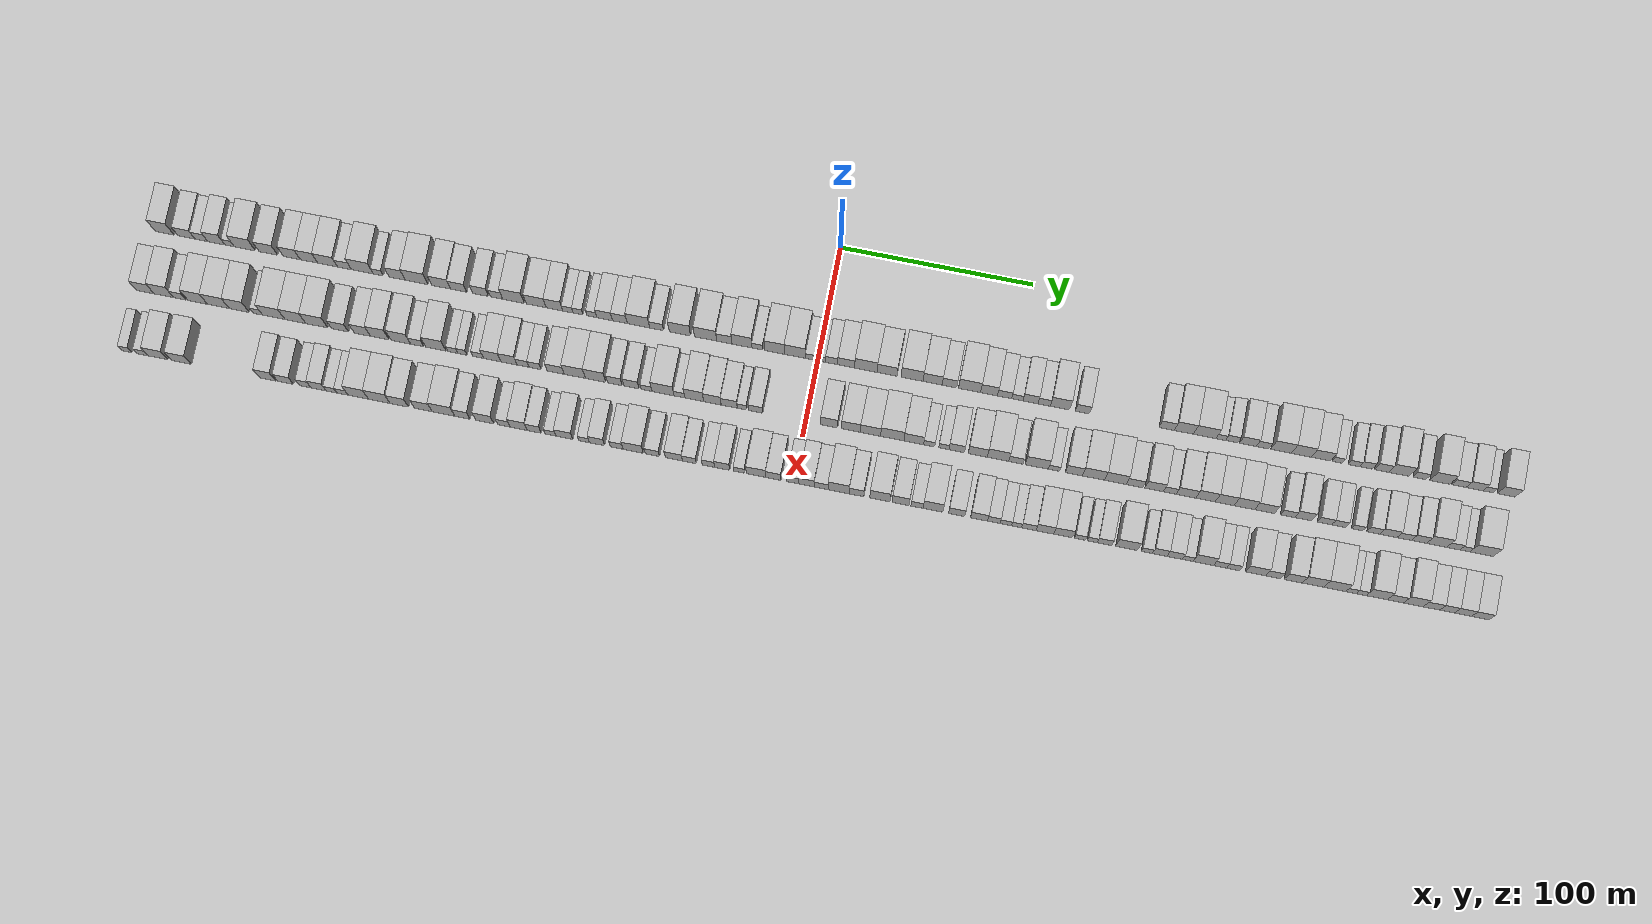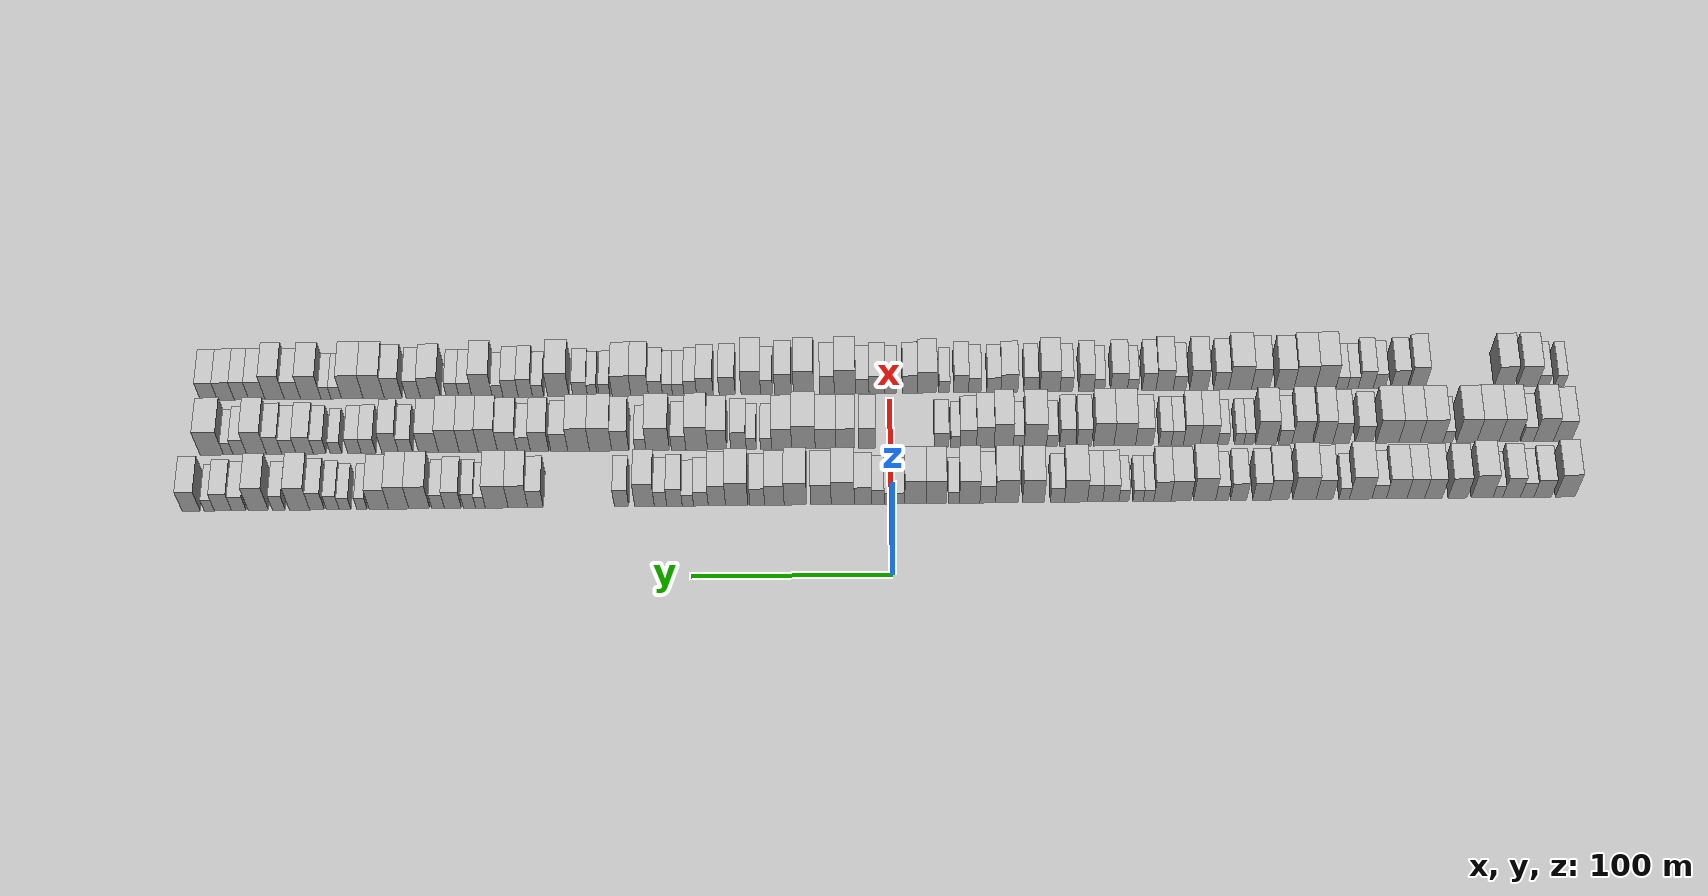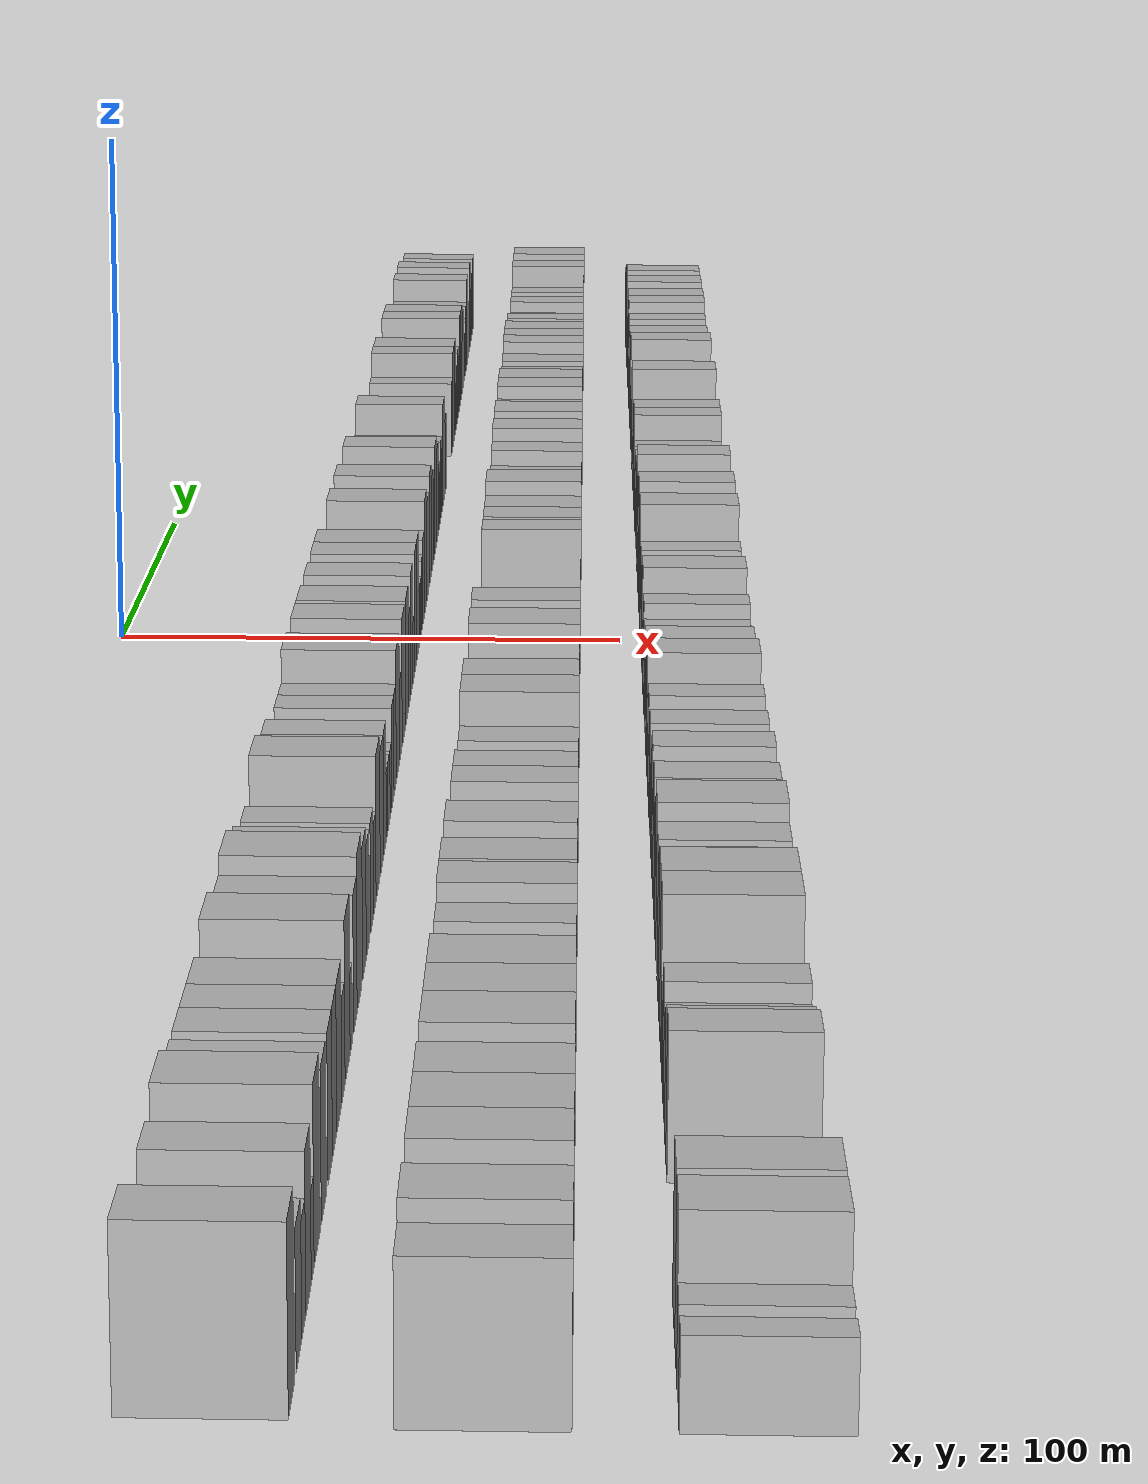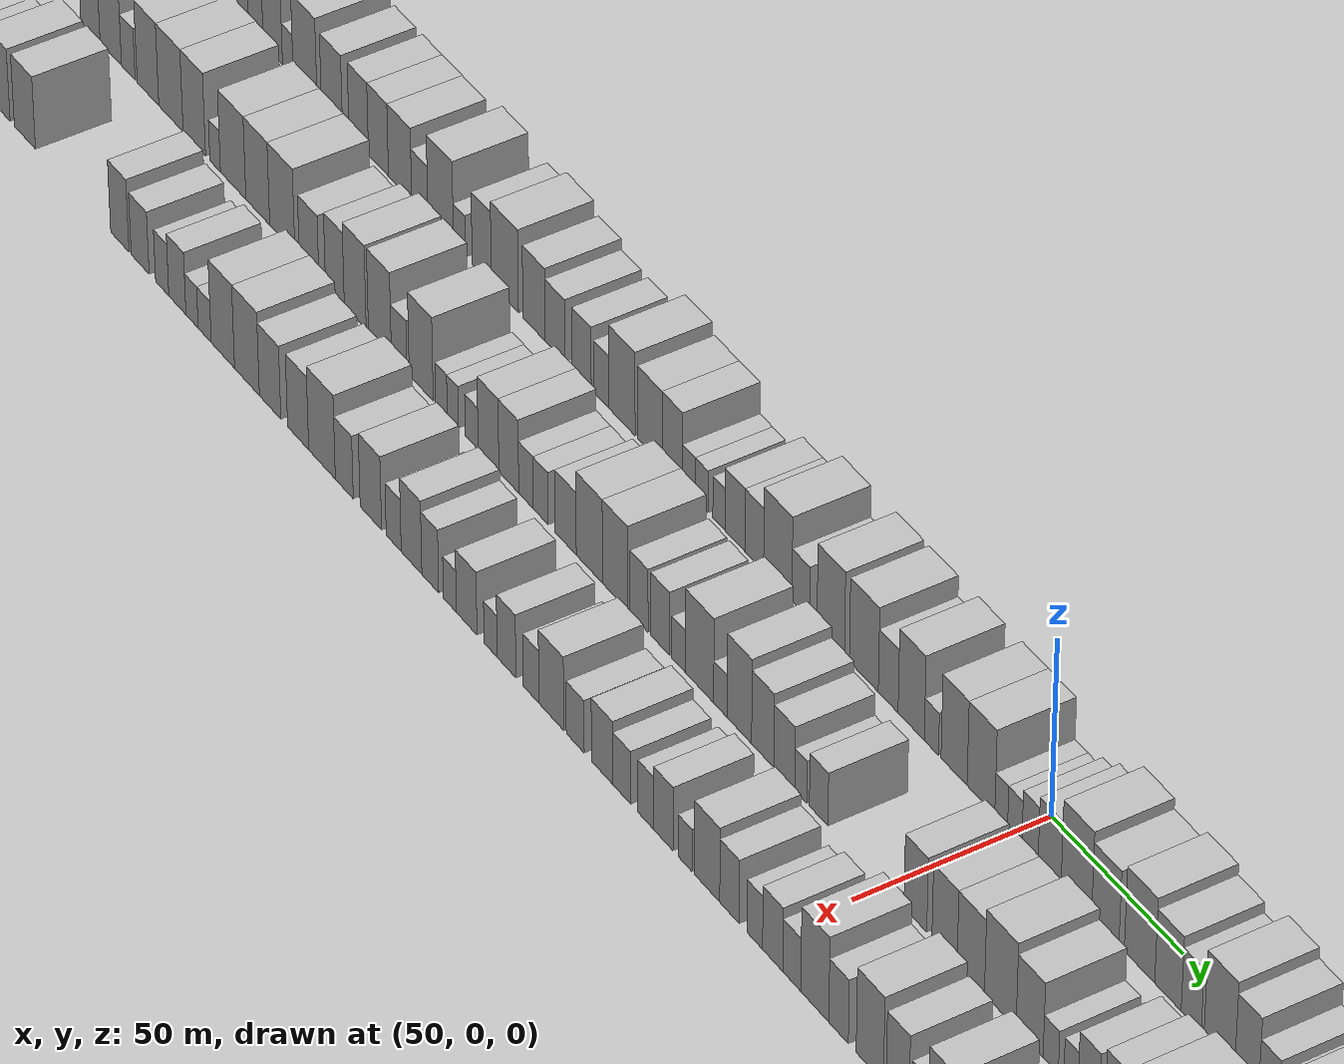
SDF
<sdf version="1.6">
 <world name="default">
  <scene>
   <sky><clouds><speed>12</speed></clouds></sky>
   <ambient>0.4 0.4 0.4 1</ambient>
   <background>0.7 0.7 0.7 1</background>
   <shadows>1</shadows>
  </scene>
  <gravity>0 0 -9.8066</gravity>
  <magnetic_field>6e-06 2.3e-05 -4.2e-05</magnetic_field>
  <physics default="0" name="default_physics" type="ode">
   <ode>
    <solver>
     <type>quick</type>
     <iters>10</iters>
     <sor>1.0</sor>
     <use_dynamic_moi_rescaling>0</use_dynamic_moi_rescaling>
    </solver>
    <constraints>
     <cfm>0</cfm>
     <erp>0.2</erp>
     <contact_max_correcting_vel>100</contact_max_correcting_vel>
     <contact_surface_layer>0.001</contact_surface_layer>
    </constraints>
   </ode>
   <max_step_size>0.004</max_step_size>
   <real_time_factor>1</real_time_factor>
   <real_time_update_rate>250</real_time_update_rate>
  </physics>
  <light name="sun" type="directional">
   <pose>0 0 10 0 0 0</pose>
   <diffuse>0.8 0.8 0.8 1</diffuse>
   <specular>0.2 0.2 0.2 1</specular>
   <attenuation>
    <range>1000</range>
    <constant>0.9</constant>
    <linear>0.01</linear>
    <quadratic>0.001</quadratic>
   </attenuation>
   <direction>-0.5 0.1 -0.9</direction>
  </light>
  <model name="building_1">
   <static>1</static>
   <pose>50.0000 -341.0320 0 0.000000 0.000000 0.000000</pose>
   <link name="link">
    <pose>0 0 12.00 0 0 0</pose>
    <collision name="collision"><geometry><box><size>20.0000 9.9359 24.0000</size></box></geometry></collision>
    <visual name="visual">
     <cast_shadows>0</cast_shadows>
     <geometry><box><size>20.0000 9.9359 24.0000</size></box></geometry>
     <material>
      <script>
       <uri>model://HANNAS_wall/materials/scripts</uri>
       <uri>model://HANNAS_wall/materials/textures</uri>
       <name>vrc/HANNAS_wall</name>
      </script>
     </material>
    </visual>
   </link>
  </model>
  <model name="building_2">
   <static>1</static>
   <pose>50.0000 -329.5887 0 0.000000 0.000000 0.000000</pose>
   <link name="link">
    <pose>0 0 9.00 0 0 0</pose>
    <collision name="collision"><geometry><box><size>20.0000 8.9509 18.0000</size></box></geometry></collision>
    <visual name="visual">
     <cast_shadows>0</cast_shadows>
     <geometry><box><size>20.0000 8.9509 18.0000</size></box></geometry>
     <material>
      <script>
       <uri>model://HANNAS_wall/materials/scripts</uri>
       <uri>model://HANNAS_wall/materials/textures</uri>
       <name>vrc/HANNAS_wall</name>
      </script>
     </material>
    </visual>
   </link>
  </model>
  <model name="building_3">
   <static>1</static>
   <pose>50.0000 -321.7223 0 0.000000 0.000000 0.000000</pose>
   <link name="link">
    <pose>0 0 7.50 0 0 0</pose>
    <collision name="collision"><geometry><box><size>20.0000 6.7819 15.0000</size></box></geometry></collision>
    <visual name="visual">
     <cast_shadows>0</cast_shadows>
     <geometry><box><size>20.0000 6.7819 15.0000</size></box></geometry>
     <material>
      <script>
       <uri>model://HANNAS_wall/materials/scripts</uri>
       <uri>model://HANNAS_wall/materials/textures</uri>
       <name>vrc/HANNAS_wall</name>
      </script>
     </material>
    </visual>
   </link>
  </model>
  <model name="building_4">
   <static>1</static>
   <pose>50.0000 -313.8562 0 0.000000 0.000000 0.000000</pose>
   <link name="link">
    <pose>0 0 10.50 0 0 0</pose>
    <collision name="collision"><geometry><box><size>20.0000 8.9503 21.0000</size></box></geometry></collision>
    <visual name="visual">
     <cast_shadows>0</cast_shadows>
     <geometry><box><size>20.0000 8.9503 21.0000</size></box></geometry>
     <material>
      <script>
       <uri>model://HANNAS_wall/materials/scripts</uri>
       <uri>model://HANNAS_wall/materials/textures</uri>
       <name>vrc/HANNAS_wall</name>
      </script>
     </material>
    </visual>
   </link>
  </model>
  <model name="building_5">
   <static>1</static>
   <pose>50.0000 -306.8981 0 0.000000 0.000000 0.000000</pose>
   <link name="link">
    <pose>0 0 6.00 0 0 0</pose>
    <collision name="collision"><geometry><box><size>20.0000 4.9658 12.0000</size></box></geometry></collision>
    <visual name="visual">
     <cast_shadows>0</cast_shadows>
     <geometry><box><size>20.0000 4.9658 12.0000</size></box></geometry>
     <material>
      <script>
       <uri>model://HANNAS_wall/materials/scripts</uri>
       <uri>model://HANNAS_wall/materials/textures</uri>
       <name>vrc/HANNAS_wall</name>
      </script>
     </material>
    </visual>
   </link>
  </model>
  <model name="building_6">
   <static>1</static>
   <pose>50.0000 -298.8900 0 0.000000 0.000000 0.000000</pose>
   <link name="link">
    <pose>0 0 12.00 0 0 0</pose>
    <collision name="collision"><geometry><box><size>20.0000 11.0505 24.0000</size></box></geometry></collision>
    <visual name="visual">
     <cast_shadows>0</cast_shadows>
     <geometry><box><size>20.0000 11.0505 24.0000</size></box></geometry>
     <material>
      <script>
       <uri>model://HANNAS_wall/materials/scripts</uri>
       <uri>model://HANNAS_wall/materials/textures</uri>
       <name>vrc/HANNAS_wall</name>
      </script>
     </material>
    </visual>
   </link>
  </model>
  <model name="building_7">
   <static>1</static>
   <pose>50.0000 -286.5290 0 0.000000 0.000000 0.000000</pose>
   <link name="link">
    <pose>0 0 10.50 0 0 0</pose>
    <collision name="collision"><geometry><box><size>20.0000 9.6714 21.0000</size></box></geometry></collision>
    <visual name="visual">
     <cast_shadows>0</cast_shadows>
     <geometry><box><size>20.0000 9.6714 21.0000</size></box></geometry>
     <material>
      <script>
       <uri>model://HANNAS_wall/materials/scripts</uri>
       <uri>model://HANNAS_wall/materials/textures</uri>
       <name>vrc/HANNAS_wall</name>
      </script>
     </material>
    </visual>
   </link>
  </model>
  <model name="building_8">
   <static>1</static>
   <pose>50.0000 -274.2663 0 0.000000 0.000000 0.000000</pose>
   <link name="link">
    <pose>0 0 10.50 0 0 0</pose>
    <collision name="collision"><geometry><box><size>20.0000 8.8541 21.0000</size></box></geometry></collision>
    <visual name="visual">
     <cast_shadows>0</cast_shadows>
     <geometry><box><size>20.0000 8.8541 21.0000</size></box></geometry>
     <material>
      <script>
       <uri>model://HANNAS_wall/materials/scripts</uri>
       <uri>model://HANNAS_wall/materials/textures</uri>
       <name>vrc/HANNAS_wall</name>
      </script>
     </material>
    </visual>
   </link>
  </model>
  <model name="building_9">
   <static>1</static>
   <pose>50.0000 -265.3142 0 0.000000 0.000000 0.000000</pose>
   <link name="link">
    <pose>0 0 10.50 0 0 0</pose>
    <collision name="collision"><geometry><box><size>20.0000 9.0501 21.0000</size></box></geometry></collision>
    <visual name="visual">
     <cast_shadows>0</cast_shadows>
     <geometry><box><size>20.0000 9.0501 21.0000</size></box></geometry>
     <material>
      <script>
       <uri>model://HANNAS_wall/materials/scripts</uri>
       <uri>model://HANNAS_wall/materials/textures</uri>
       <name>vrc/HANNAS_wall</name>
      </script>
     </material>
    </visual>
   </link>
  </model>
  <model name="building_10">
   <static>1</static>
   <pose>50.0000 -255.5468 0 0.000000 0.000000 0.000000</pose>
   <link name="link">
    <pose>0 0 10.50 0 0 0</pose>
    <collision name="collision"><geometry><box><size>20.0000 10.4847 21.0000</size></box></geometry></collision>
    <visual name="visual">
     <cast_shadows>0</cast_shadows>
     <geometry><box><size>20.0000 10.4847 21.0000</size></box></geometry>
     <material>
      <script>
       <uri>model://HANNAS_wall/materials/scripts</uri>
       <uri>model://HANNAS_wall/materials/textures</uri>
       <name>vrc/HANNAS_wall</name>
      </script>
     </material>
    </visual>
   </link>
  </model>
  <model name="building_11">
   <static>1</static>
   <pose>50.0000 -246.6663 0 0.000000 0.000000 0.000000</pose>
   <link name="link">
    <pose>0 0 7.50 0 0 0</pose>
    <collision name="collision"><geometry><box><size>20.0000 7.2763 15.0000</size></box></geometry></collision>
    <visual name="visual">
     <cast_shadows>0</cast_shadows>
     <geometry><box><size>20.0000 7.2763 15.0000</size></box></geometry>
     <material>
      <script>
       <uri>model://HANNAS_wall/materials/scripts</uri>
       <uri>model://HANNAS_wall/materials/textures</uri>
       <name>vrc/HANNAS_wall</name>
      </script>
     </material>
    </visual>
   </link>
  </model>
  <model name="building_12">
   <static>1</static>
   <pose>50.0000 -237.3181 0 0.000000 0.000000 0.000000</pose>
   <link name="link">
    <pose>0 0 12.00 0 0 0</pose>
    <collision name="collision"><geometry><box><size>20.0000 11.4202 24.0000</size></box></geometry></collision>
    <visual name="visual">
     <cast_shadows>0</cast_shadows>
     <geometry><box><size>20.0000 11.4202 24.0000</size></box></geometry>
     <material>
      <script>
       <uri>model://HANNAS_wall/materials/scripts</uri>
       <uri>model://HANNAS_wall/materials/textures</uri>
       <name>vrc/HANNAS_wall</name>
      </script>
     </material>
    </visual>
   </link>
  </model>
  <model name="building_13">
   <static>1</static>
   <pose>50.0000 -228.9586 0 0.000000 0.000000 0.000000</pose>
   <link name="link">
    <pose>0 0 6.00 0 0 0</pose>
    <collision name="collision"><geometry><box><size>20.0000 5.2988 12.0000</size></box></geometry></collision>
    <visual name="visual">
     <cast_shadows>0</cast_shadows>
     <geometry><box><size>20.0000 5.2988 12.0000</size></box></geometry>
     <material>
      <script>
       <uri>model://HANNAS_wall/materials/scripts</uri>
       <uri>model://HANNAS_wall/materials/textures</uri>
       <name>vrc/HANNAS_wall</name>
      </script>
     </material>
    </visual>
   </link>
  </model>
  <model name="building_14">
   <static>1</static>
   <pose>50.0000 -219.0519 0 0.000000 0.000000 0.000000</pose>
   <link name="link">
    <pose>0 0 10.50 0 0 0</pose>
    <collision name="collision"><geometry><box><size>20.0000 8.5146 21.0000</size></box></geometry></collision>
    <visual name="visual">
     <cast_shadows>0</cast_shadows>
     <geometry><box><size>20.0000 8.5146 21.0000</size></box></geometry>
     <material>
      <script>
       <uri>model://HANNAS_wall/materials/scripts</uri>
       <uri>model://HANNAS_wall/materials/textures</uri>
       <name>vrc/HANNAS_wall</name>
      </script>
     </material>
    </visual>
   </link>
  </model>
  <model name="building_15">
   <static>1</static>
   <pose>50.0000 -208.8753 0 0.000000 0.000000 0.000000</pose>
   <link name="link">
    <pose>0 0 12.00 0 0 0</pose>
    <collision name="collision"><geometry><box><size>20.0000 11.8385 24.0000</size></box></geometry></collision>
    <visual name="visual">
     <cast_shadows>0</cast_shadows>
     <geometry><box><size>20.0000 11.8385 24.0000</size></box></geometry>
     <material>
      <script>
       <uri>model://HANNAS_wall/materials/scripts</uri>
       <uri>model://HANNAS_wall/materials/textures</uri>
       <name>vrc/HANNAS_wall</name>
      </script>
     </material>
    </visual>
   </link>
  </model>
  <model name="building_16">
   <static>1</static>
   <pose>50.0000 -196.1090 0 0.000000 0.000000 0.000000</pose>
   <link name="link">
    <pose>0 0 10.50 0 0 0</pose>
    <collision name="collision"><geometry><box><size>20.0000 9.6940 21.0000</size></box></geometry></collision>
    <visual name="visual">
     <cast_shadows>0</cast_shadows>
     <geometry><box><size>20.0000 9.6940 21.0000</size></box></geometry>
     <material>
      <script>
       <uri>model://HANNAS_wall/materials/scripts</uri>
       <uri>model://HANNAS_wall/materials/textures</uri>
       <name>vrc/HANNAS_wall</name>
      </script>
     </material>
    </visual>
   </link>
  </model>
  <model name="building_17">
   <static>1</static>
   <pose>50.0000 -186.9708 0 0.000000 0.000000 0.000000</pose>
   <link name="link">
    <pose>0 0 9.00 0 0 0</pose>
    <collision name="collision"><geometry><box><size>20.0000 8.5825 18.0000</size></box></geometry></collision>
    <visual name="visual">
     <cast_shadows>0</cast_shadows>
     <geometry><box><size>20.0000 8.5825 18.0000</size></box></geometry>
     <material>
      <script>
       <uri>model://HANNAS_wall/materials/scripts</uri>
       <uri>model://HANNAS_wall/materials/textures</uri>
       <name>vrc/HANNAS_wall</name>
      </script>
     </material>
    </visual>
   </link>
  </model>
  <model name="building_18">
   <static>1</static>
   <pose>50.0000 -175.5464 0 0.000000 0.000000 0.000000</pose>
   <link name="link">
    <pose>0 0 9.00 0 0 0</pose>
    <collision name="collision"><geometry><box><size>20.0000 8.2664 18.0000</size></box></geometry></collision>
    <visual name="visual">
     <cast_shadows>0</cast_shadows>
     <geometry><box><size>20.0000 8.2664 18.0000</size></box></geometry>
     <material>
      <script>
       <uri>model://HANNAS_wall/materials/scripts</uri>
       <uri>model://HANNAS_wall/materials/textures</uri>
       <name>vrc/HANNAS_wall</name>
      </script>
     </material>
    </visual>
   </link>
  </model>
  <model name="building_19">
   <static>1</static>
   <pose>50.0000 -167.1778 0 0.000000 0.000000 0.000000</pose>
   <link name="link">
    <pose>0 0 7.50 0 0 0</pose>
    <collision name="collision"><geometry><box><size>20.0000 6.4707 15.0000</size></box></geometry></collision>
    <visual name="visual">
     <cast_shadows>0</cast_shadows>
     <geometry><box><size>20.0000 6.4707 15.0000</size></box></geometry>
     <material>
      <script>
       <uri>model://HANNAS_wall/materials/scripts</uri>
       <uri>model://HANNAS_wall/materials/textures</uri>
       <name>vrc/HANNAS_wall</name>
      </script>
     </material>
    </visual>
   </link>
  </model>
  <model name="building_20">
   <static>1</static>
   <pose>50.0000 -158.3148 0 0.000000 0.000000 0.000000</pose>
   <link name="link">
    <pose>0 0 12.00 0 0 0</pose>
    <collision name="collision"><geometry><box><size>20.0000 11.2554 24.0000</size></box></geometry></collision>
    <visual name="visual">
     <cast_shadows>0</cast_shadows>
     <geometry><box><size>20.0000 11.2554 24.0000</size></box></geometry>
     <material>
      <script>
       <uri>model://HANNAS_wall/materials/scripts</uri>
       <uri>model://HANNAS_wall/materials/textures</uri>
       <name>vrc/HANNAS_wall</name>
      </script>
     </material>
    </visual>
   </link>
  </model>
  <model name="building_21">
   <static>1</static>
   <pose>50.0000 -146.4934 0 0.000000 0.000000 0.000000</pose>
   <link name="link">
    <pose>0 0 10.50 0 0 0</pose>
    <collision name="collision"><geometry><box><size>20.0000 10.3874 21.0000</size></box></geometry></collision>
    <visual name="visual">
     <cast_shadows>0</cast_shadows>
     <geometry><box><size>20.0000 10.3874 21.0000</size></box></geometry>
     <material>
      <script>
       <uri>model://HANNAS_wall/materials/scripts</uri>
       <uri>model://HANNAS_wall/materials/textures</uri>
       <name>vrc/HANNAS_wall</name>
      </script>
     </material>
    </visual>
   </link>
  </model>
  <model name="building_22">
   <static>1</static>
   <pose>50.0000 -136.9624 0 0.000000 0.000000 0.000000</pose>
   <link name="link">
    <pose>0 0 10.50 0 0 0</pose>
    <collision name="collision"><geometry><box><size>20.0000 8.6745 21.0000</size></box></geometry></collision>
    <visual name="visual">
     <cast_shadows>0</cast_shadows>
     <geometry><box><size>20.0000 8.6745 21.0000</size></box></geometry>
     <material>
      <script>
       <uri>model://HANNAS_wall/materials/scripts</uri>
       <uri>model://HANNAS_wall/materials/textures</uri>
       <name>vrc/HANNAS_wall</name>
      </script>
     </material>
    </visual>
   </link>
  </model>
  <model name="building_23">
   <static>1</static>
   <pose>50.0000 -129.9868 0 0.000000 0.000000 0.000000</pose>
   <link name="link">
    <pose>0 0 6.00 0 0 0</pose>
    <collision name="collision"><geometry><box><size>20.0000 5.2768 12.0000</size></box></geometry></collision>
    <visual name="visual">
     <cast_shadows>0</cast_shadows>
     <geometry><box><size>20.0000 5.2768 12.0000</size></box></geometry>
     <material>
      <script>
       <uri>model://HANNAS_wall/materials/scripts</uri>
       <uri>model://HANNAS_wall/materials/textures</uri>
       <name>vrc/HANNAS_wall</name>
      </script>
     </material>
    </visual>
   </link>
  </model>
  <model name="building_24">
   <static>1</static>
   <pose>50.0000 -124.6941 0 0.000000 0.000000 0.000000</pose>
   <link name="link">
    <pose>0 0 6.00 0 0 0</pose>
    <collision name="collision"><geometry><box><size>20.0000 5.3085 12.0000</size></box></geometry></collision>
    <visual name="visual">
     <cast_shadows>0</cast_shadows>
     <geometry><box><size>20.0000 5.3085 12.0000</size></box></geometry>
     <material>
      <script>
       <uri>model://HANNAS_wall/materials/scripts</uri>
       <uri>model://HANNAS_wall/materials/textures</uri>
       <name>vrc/HANNAS_wall</name>
      </script>
     </material>
    </visual>
   </link>
  </model>
  <model name="building_25">
   <static>1</static>
   <pose>50.0000 -117.5120 0 0.000000 0.000000 0.000000</pose>
   <link name="link">
    <pose>0 0 6.00 0 0 0</pose>
    <collision name="collision"><geometry><box><size>20.0000 5.0557 12.0000</size></box></geometry></collision>
    <visual name="visual">
     <cast_shadows>0</cast_shadows>
     <geometry><box><size>20.0000 5.0557 12.0000</size></box></geometry>
     <material>
      <script>
       <uri>model://HANNAS_wall/materials/scripts</uri>
       <uri>model://HANNAS_wall/materials/textures</uri>
       <name>vrc/HANNAS_wall</name>
      </script>
     </material>
    </visual>
   </link>
  </model>
  <model name="building_26">
   <static>1</static>
   <pose>50.0000 -110.8782 0 0.000000 0.000000 0.000000</pose>
   <link name="link">
    <pose>0 0 9.00 0 0 0</pose>
    <collision name="collision"><geometry><box><size>20.0000 8.2120 18.0000</size></box></geometry></collision>
    <visual name="visual">
     <cast_shadows>0</cast_shadows>
     <geometry><box><size>20.0000 8.2120 18.0000</size></box></geometry>
     <material>
      <script>
       <uri>model://HANNAS_wall/materials/scripts</uri>
       <uri>model://HANNAS_wall/materials/textures</uri>
       <name>vrc/HANNAS_wall</name>
      </script>
     </material>
    </visual>
   </link>
  </model>
  <model name="building_27">
   <static>1</static>
   <pose>50.0000 -102.9081 0 0.000000 0.000000 0.000000</pose>
   <link name="link">
    <pose>0 0 9.00 0 0 0</pose>
    <collision name="collision"><geometry><box><size>20.0000 7.7282 18.0000</size></box></geometry></collision>
    <visual name="visual">
     <cast_shadows>0</cast_shadows>
     <geometry><box><size>20.0000 7.7282 18.0000</size></box></geometry>
     <material>
      <script>
       <uri>model://HANNAS_wall/materials/scripts</uri>
       <uri>model://HANNAS_wall/materials/textures</uri>
       <name>vrc/HANNAS_wall</name>
      </script>
     </material>
    </visual>
   </link>
  </model>
  <model name="building_28">
   <static>1</static>
   <pose>50.0000 -93.2294 0 0.000000 0.000000 0.000000</pose>
   <link name="link">
    <pose>0 0 12.00 0 0 0</pose>
    <collision name="collision"><geometry><box><size>20.0000 11.6291 24.0000</size></box></geometry></collision>
    <visual name="visual">
     <cast_shadows>0</cast_shadows>
     <geometry><box><size>20.0000 11.6291 24.0000</size></box></geometry>
     <material>
      <script>
       <uri>model://HANNAS_wall/materials/scripts</uri>
       <uri>model://HANNAS_wall/materials/textures</uri>
       <name>vrc/HANNAS_wall</name>
      </script>
     </material>
    </visual>
   </link>
  </model>
  <model name="building_29">
   <static>1</static>
   <pose>50.0000 -83.8291 0 0.000000 0.000000 0.000000</pose>
   <link name="link">
    <pose>0 0 7.50 0 0 0</pose>
    <collision name="collision"><geometry><box><size>20.0000 7.1716 15.0000</size></box></geometry></collision>
    <visual name="visual">
     <cast_shadows>0</cast_shadows>
     <geometry><box><size>20.0000 7.1716 15.0000</size></box></geometry>
     <material>
      <script>
       <uri>model://HANNAS_wall/materials/scripts</uri>
       <uri>model://HANNAS_wall/materials/textures</uri>
       <name>vrc/HANNAS_wall</name>
      </script>
     </material>
    </visual>
   </link>
  </model>
  <model name="building_30">
   <static>1</static>
   <pose>50.0000 -71.7021 0 0.000000 0.000000 0.000000</pose>
   <link name="link">
    <pose>0 0 12.00 0 0 0</pose>
    <collision name="collision"><geometry><box><size>20.0000 11.0824 24.0000</size></box></geometry></collision>
    <visual name="visual">
     <cast_shadows>0</cast_shadows>
     <geometry><box><size>20.0000 11.0824 24.0000</size></box></geometry>
     <material>
      <script>
       <uri>model://HANNAS_wall/materials/scripts</uri>
       <uri>model://HANNAS_wall/materials/textures</uri>
       <name>vrc/HANNAS_wall</name>
      </script>
     </material>
    </visual>
   </link>
  </model>
  <model name="building_31">
   <static>1</static>
   <pose>50.0000 -58.3676 0 0.000000 0.000000 0.000000</pose>
   <link name="link">
    <pose>0 0 12.00 0 0 0</pose>
    <collision name="collision"><geometry><box><size>20.0000 11.5866 24.0000</size></box></geometry></collision>
    <visual name="visual">
     <cast_shadows>0</cast_shadows>
     <geometry><box><size>20.0000 11.5866 24.0000</size></box></geometry>
     <material>
      <script>
       <uri>model://HANNAS_wall/materials/scripts</uri>
       <uri>model://HANNAS_wall/materials/textures</uri>
       <name>vrc/HANNAS_wall</name>
      </script>
     </material>
    </visual>
   </link>
  </model>
  <model name="building_32">
   <static>1</static>
   <pose>50.0000 -48.6234 0 0.000000 0.000000 0.000000</pose>
   <link name="link">
    <pose>0 0 9.00 0 0 0</pose>
    <collision name="collision"><geometry><box><size>20.0000 7.9017 18.0000</size></box></geometry></collision>
    <visual name="visual">
     <cast_shadows>0</cast_shadows>
     <geometry><box><size>20.0000 7.9017 18.0000</size></box></geometry>
     <material>
      <script>
       <uri>model://HANNAS_wall/materials/scripts</uri>
       <uri>model://HANNAS_wall/materials/textures</uri>
       <name>vrc/HANNAS_wall</name>
      </script>
     </material>
    </visual>
   </link>
  </model>
  <model name="building_33">
   <static>1</static>
   <pose>50.0000 -39.4885 0 0.000000 0.000000 0.000000</pose>
   <link name="link">
    <pose>0 0 12.00 0 0 0</pose>
    <collision name="collision"><geometry><box><size>20.0000 10.3681 24.0000</size></box></geometry></collision>
    <visual name="visual">
     <cast_shadows>0</cast_shadows>
     <geometry><box><size>20.0000 10.3681 24.0000</size></box></geometry>
     <material>
      <script>
       <uri>model://HANNAS_wall/materials/scripts</uri>
       <uri>model://HANNAS_wall/materials/textures</uri>
       <name>vrc/HANNAS_wall</name>
      </script>
     </material>
    </visual>
   </link>
  </model>
  <model name="building_34">
   <static>1</static>
   <pose>50.0000 -31.4960 0 0.000000 0.000000 0.000000</pose>
   <link name="link">
    <pose>0 0 6.00 0 0 0</pose>
    <collision name="collision"><geometry><box><size>20.0000 5.6169 12.0000</size></box></geometry></collision>
    <visual name="visual">
     <cast_shadows>0</cast_shadows>
     <geometry><box><size>20.0000 5.6169 12.0000</size></box></geometry>
     <material>
      <script>
       <uri>model://HANNAS_wall/materials/scripts</uri>
       <uri>model://HANNAS_wall/materials/textures</uri>
       <name>vrc/HANNAS_wall</name>
      </script>
     </material>
    </visual>
   </link>
  </model>
  <model name="building_35">
   <static>1</static>
   <pose>50.0000 -22.5851 0 0.000000 0.000000 0.000000</pose>
   <link name="link">
    <pose>0 0 12.00 0 0 0</pose>
    <collision name="collision"><geometry><box><size>20.0000 10.2047 24.0000</size></box></geometry></collision>
    <visual name="visual">
     <cast_shadows>0</cast_shadows>
     <geometry><box><size>20.0000 10.2047 24.0000</size></box></geometry>
     <material>
      <script>
       <uri>model://HANNAS_wall/materials/scripts</uri>
       <uri>model://HANNAS_wall/materials/textures</uri>
       <name>vrc/HANNAS_wall</name>
      </script>
     </material>
    </visual>
   </link>
  </model>
  <model name="building_36">
   <static>1</static>
   <pose>50.0000 -12.0826 0 0.000000 0.000000 0.000000</pose>
   <link name="link">
    <pose>0 0 12.00 0 0 0</pose>
    <collision name="collision"><geometry><box><size>20.0000 10.8003 24.0000</size></box></geometry></collision>
    <visual name="visual">
     <cast_shadows>0</cast_shadows>
     <geometry><box><size>20.0000 10.8003 24.0000</size></box></geometry>
     <material>
      <script>
       <uri>model://HANNAS_wall/materials/scripts</uri>
       <uri>model://HANNAS_wall/materials/textures</uri>
       <name>vrc/HANNAS_wall</name>
      </script>
     </material>
    </visual>
   </link>
  </model>
  <model name="building_37">
   <static>1</static>
   <pose>50.0000 -4.2004 0 0.000000 0.000000 0.000000</pose>
   <link name="link">
    <pose>0 0 6.00 0 0 0</pose>
    <collision name="collision"><geometry><box><size>20.0000 4.9642 12.0000</size></box></geometry></collision>
    <visual name="visual">
     <cast_shadows>0</cast_shadows>
     <geometry><box><size>20.0000 4.9642 12.0000</size></box></geometry>
     <material>
      <script>
       <uri>model://HANNAS_wall/materials/scripts</uri>
       <uri>model://HANNAS_wall/materials/textures</uri>
       <name>vrc/HANNAS_wall</name>
      </script>
     </material>
    </visual>
   </link>
  </model>
  <model name="building_38">
   <static>1</static>
   <pose>50.0000 1.0541 0 0.000000 0.000000 0.000000</pose>
   <link name="link">
    <pose>0 0 6.00 0 0 0</pose>
    <collision name="collision"><geometry><box><size>20.0000 5.5447 12.0000</size></box></geometry></collision>
    <visual name="visual">
     <cast_shadows>0</cast_shadows>
     <geometry><box><size>20.0000 5.5447 12.0000</size></box></geometry>
     <material>
      <script>
       <uri>model://HANNAS_wall/materials/scripts</uri>
       <uri>model://HANNAS_wall/materials/textures</uri>
       <name>vrc/HANNAS_wall</name>
      </script>
     </material>
    </visual>
   </link>
  </model>
  <model name="building_39">
   <static>1</static>
   <pose>50.0000 6.9536 0 0.000000 0.000000 0.000000</pose>
   <link name="link">
    <pose>0 0 7.50 0 0 0</pose>
    <collision name="collision"><geometry><box><size>20.0000 6.2543 15.0000</size></box></geometry></collision>
    <visual name="visual">
     <cast_shadows>0</cast_shadows>
     <geometry><box><size>20.0000 6.2543 15.0000</size></box></geometry>
     <material>
      <script>
       <uri>model://HANNAS_wall/materials/scripts</uri>
       <uri>model://HANNAS_wall/materials/textures</uri>
       <name>vrc/HANNAS_wall</name>
      </script>
     </material>
    </visual>
   </link>
  </model>
  <model name="building_40">
   <static>1</static>
   <pose>50.0000 14.4750 0 0.000000 0.000000 0.000000</pose>
   <link name="link">
    <pose>0 0 9.00 0 0 0</pose>
    <collision name="collision"><geometry><box><size>20.0000 8.7886 18.0000</size></box></geometry></collision>
    <visual name="visual">
     <cast_shadows>0</cast_shadows>
     <geometry><box><size>20.0000 8.7886 18.0000</size></box></geometry>
     <material>
      <script>
       <uri>model://HANNAS_wall/materials/scripts</uri>
       <uri>model://HANNAS_wall/materials/textures</uri>
       <name>vrc/HANNAS_wall</name>
      </script>
     </material>
    </visual>
   </link>
  </model>
  <model name="building_41">
   <static>1</static>
   <pose>50.0000 24.6929 0 0.000000 0.000000 0.000000</pose>
   <link name="link">
    <pose>0 0 12.00 0 0 0</pose>
    <collision name="collision"><geometry><box><size>20.0000 11.6471 24.0000</size></box></geometry></collision>
    <visual name="visual">
     <cast_shadows>0</cast_shadows>
     <geometry><box><size>20.0000 11.6471 24.0000</size></box></geometry>
     <material>
      <script>
       <uri>model://HANNAS_wall/materials/scripts</uri>
       <uri>model://HANNAS_wall/materials/textures</uri>
       <name>vrc/HANNAS_wall</name>
      </script>
     </material>
    </visual>
   </link>
  </model>
  <model name="building_42">
   <static>1</static>
   <pose>50.0000 35.6729 0 0.000000 0.000000 0.000000</pose>
   <link name="link">
    <pose>0 0 10.50 0 0 0</pose>
    <collision name="collision"><geometry><box><size>20.0000 10.3129 21.0000</size></box></geometry></collision>
    <visual name="visual">
     <cast_shadows>0</cast_shadows>
     <geometry><box><size>20.0000 10.3129 21.0000</size></box></geometry>
     <material>
      <script>
       <uri>model://HANNAS_wall/materials/scripts</uri>
       <uri>model://HANNAS_wall/materials/textures</uri>
       <name>vrc/HANNAS_wall</name>
      </script>
     </material>
    </visual>
   </link>
  </model>
  <model name="building_43">
   <static>1</static>
   <pose>50.0000 48.5430 0 0.000000 0.000000 0.000000</pose>
   <link name="link">
    <pose>0 0 12.00 0 0 0</pose>
    <collision name="collision"><geometry><box><size>20.0000 11.4274 24.0000</size></box></geometry></collision>
    <visual name="visual">
     <cast_shadows>0</cast_shadows>
     <geometry><box><size>20.0000 11.4274 24.0000</size></box></geometry>
     <material>
      <script>
       <uri>model://HANNAS_wall/materials/scripts</uri>
       <uri>model://HANNAS_wall/materials/textures</uri>
       <name>vrc/HANNAS_wall</name>
      </script>
     </material>
    </visual>
   </link>
  </model>
  <model name="building_44">
   <static>1</static>
   <pose>50.0000 59.1846 0 0.000000 0.000000 0.000000</pose>
   <link name="link">
    <pose>0 0 10.50 0 0 0</pose>
    <collision name="collision"><geometry><box><size>20.0000 9.8557 21.0000</size></box></geometry></collision>
    <visual name="visual">
     <cast_shadows>0</cast_shadows>
     <geometry><box><size>20.0000 9.8557 21.0000</size></box></geometry>
     <material>
      <script>
       <uri>model://HANNAS_wall/materials/scripts</uri>
       <uri>model://HANNAS_wall/materials/textures</uri>
       <name>vrc/HANNAS_wall</name>
      </script>
     </material>
    </visual>
   </link>
  </model>
  <model name="building_45">
   <static>1</static>
   <pose>50.0000 67.8350 0 0.000000 0.000000 0.000000</pose>
   <link name="link">
    <pose>0 0 9.00 0 0 0</pose>
    <collision name="collision"><geometry><box><size>20.0000 7.4450 18.0000</size></box></geometry></collision>
    <visual name="visual">
     <cast_shadows>0</cast_shadows>
     <geometry><box><size>20.0000 7.4450 18.0000</size></box></geometry>
     <material>
      <script>
       <uri>model://HANNAS_wall/materials/scripts</uri>
       <uri>model://HANNAS_wall/materials/textures</uri>
       <name>vrc/HANNAS_wall</name>
      </script>
     </material>
    </visual>
   </link>
  </model>
  <model name="building_46">
   <static>1</static>
   <pose>50.0000 78.2285 0 0.000000 0.000000 0.000000</pose>
   <link name="link">
    <pose>0 0 12.00 0 0 0</pose>
    <collision name="collision"><geometry><box><size>20.0000 11.3419 24.0000</size></box></geometry></collision>
    <visual name="visual">
     <cast_shadows>0</cast_shadows>
     <geometry><box><size>20.0000 11.3419 24.0000</size></box></geometry>
     <material>
      <script>
       <uri>model://HANNAS_wall/materials/scripts</uri>
       <uri>model://HANNAS_wall/materials/textures</uri>
       <name>vrc/HANNAS_wall</name>
      </script>
     </material>
    </visual>
   </link>
  </model>
  <model name="building_47">
   <static>1</static>
   <pose>50.0000 88.2639 0 0.000000 0.000000 0.000000</pose>
   <link name="link">
    <pose>0 0 10.50 0 0 0</pose>
    <collision name="collision"><geometry><box><size>20.0000 8.7290 21.0000</size></box></geometry></collision>
    <visual name="visual">
     <cast_shadows>0</cast_shadows>
     <geometry><box><size>20.0000 8.7290 21.0000</size></box></geometry>
     <material>
      <script>
       <uri>model://HANNAS_wall/materials/scripts</uri>
       <uri>model://HANNAS_wall/materials/textures</uri>
       <name>vrc/HANNAS_wall</name>
      </script>
     </material>
    </visual>
   </link>
  </model>
  <model name="building_48">
   <static>1</static>
   <pose>50.0000 96.3212 0 0.000000 0.000000 0.000000</pose>
   <link name="link">
    <pose>0 0 7.50 0 0 0</pose>
    <collision name="collision"><geometry><box><size>20.0000 7.3855 15.0000</size></box></geometry></collision>
    <visual name="visual">
     <cast_shadows>0</cast_shadows>
     <geometry><box><size>20.0000 7.3855 15.0000</size></box></geometry>
     <material>
      <script>
       <uri>model://HANNAS_wall/materials/scripts</uri>
       <uri>model://HANNAS_wall/materials/textures</uri>
       <name>vrc/HANNAS_wall</name>
      </script>
     </material>
    </visual>
   </link>
  </model>
  <model name="building_49">
   <static>1</static>
   <pose>50.0000 102.8919 0 0.000000 0.000000 0.000000</pose>
   <link name="link">
    <pose>0 0 6.00 0 0 0</pose>
    <collision name="collision"><geometry><box><size>20.0000 5.7560 12.0000</size></box></geometry></collision>
    <visual name="visual">
     <cast_shadows>0</cast_shadows>
     <geometry><box><size>20.0000 5.7560 12.0000</size></box></geometry>
     <material>
      <script>
       <uri>model://HANNAS_wall/materials/scripts</uri>
       <uri>model://HANNAS_wall/materials/textures</uri>
       <name>vrc/HANNAS_wall</name>
      </script>
     </material>
    </visual>
   </link>
  </model>
  <model name="building_50">
   <static>1</static>
   <pose>50.0000 109.6371 0 0.000000 0.000000 0.000000</pose>
   <link name="link">
    <pose>0 0 9.00 0 0 0</pose>
    <collision name="collision"><geometry><box><size>20.0000 7.7343 18.0000</size></box></geometry></collision>
    <visual name="visual">
     <cast_shadows>0</cast_shadows>
     <geometry><box><size>20.0000 7.7343 18.0000</size></box></geometry>
     <material>
      <script>
       <uri>model://HANNAS_wall/materials/scripts</uri>
       <uri>model://HANNAS_wall/materials/textures</uri>
       <name>vrc/HANNAS_wall</name>
      </script>
     </material>
    </visual>
   </link>
  </model>
  <model name="building_51">
   <static>1</static>
   <pose>50.0000 116.6719 0 0.000000 0.000000 0.000000</pose>
   <link name="link">
    <pose>0 0 7.50 0 0 0</pose>
    <collision name="collision"><geometry><box><size>20.0000 6.3353 15.0000</size></box></geometry></collision>
    <visual name="visual">
     <cast_shadows>0</cast_shadows>
     <geometry><box><size>20.0000 6.3353 15.0000</size></box></geometry>
     <material>
      <script>
       <uri>model://HANNAS_wall/materials/scripts</uri>
       <uri>model://HANNAS_wall/materials/textures</uri>
       <name>vrc/HANNAS_wall</name>
      </script>
     </material>
    </visual>
   </link>
  </model>
  <model name="building_52">
   <static>1</static>
   <pose>50.0000 124.7940 0 0.000000 0.000000 0.000000</pose>
   <link name="link">
    <pose>0 0 12.00 0 0 0</pose>
    <collision name="collision"><geometry><box><size>20.0000 9.9088 24.0000</size></box></geometry></collision>
    <visual name="visual">
     <cast_shadows>0</cast_shadows>
     <geometry><box><size>20.0000 9.9088 24.0000</size></box></geometry>
     <material>
      <script>
       <uri>model://HANNAS_wall/materials/scripts</uri>
       <uri>model://HANNAS_wall/materials/textures</uri>
       <name>vrc/HANNAS_wall</name>
      </script>
     </material>
    </visual>
   </link>
  </model>
  <model name="building_53">
   <static>1</static>
   <pose>50.0000 136.3859 0 0.000000 0.000000 0.000000</pose>
   <link name="link">
    <pose>0 0 9.00 0 0 0</pose>
    <collision name="collision"><geometry><box><size>20.0000 7.2751 18.0000</size></box></geometry></collision>
    <visual name="visual">
     <cast_shadows>0</cast_shadows>
     <geometry><box><size>20.0000 7.2751 18.0000</size></box></geometry>
     <material>
      <script>
       <uri>model://HANNAS_wall/materials/scripts</uri>
       <uri>model://HANNAS_wall/materials/textures</uri>
       <name>vrc/HANNAS_wall</name>
      </script>
     </material>
    </visual>
   </link>
  </model>
  <model name="building_54">
   <static>1</static>
   <pose>50.0000 179.7932 0 0.000000 0.000000 0.000000</pose>
   <link name="link">
    <pose>0 0 9.00 0 0 0</pose>
    <collision name="collision"><geometry><box><size>20.0000 7.8465 18.0000</size></box></geometry></collision>
    <visual name="visual">
     <cast_shadows>0</cast_shadows>
     <geometry><box><size>20.0000 7.8465 18.0000</size></box></geometry>
     <material>
      <script>
       <uri>model://HANNAS_wall/materials/scripts</uri>
       <uri>model://HANNAS_wall/materials/textures</uri>
       <name>vrc/HANNAS_wall</name>
      </script>
     </material>
    </visual>
   </link>
  </model>
  <model name="building_55">
   <static>1</static>
   <pose>50.0000 188.6516 0 0.000000 0.000000 0.000000</pose>
   <link name="link">
    <pose>0 0 12.00 0 0 0</pose>
    <collision name="collision"><geometry><box><size>20.0000 9.8704 24.0000</size></box></geometry></collision>
    <visual name="visual">
     <cast_shadows>0</cast_shadows>
     <geometry><box><size>20.0000 9.8704 24.0000</size></box></geometry>
     <material>
      <script>
       <uri>model://HANNAS_wall/materials/scripts</uri>
       <uri>model://HANNAS_wall/materials/textures</uri>
       <name>vrc/HANNAS_wall</name>
      </script>
     </material>
    </visual>
   </link>
  </model>
  <model name="building_56">
   <static>1</static>
   <pose>50.0000 199.3849 0 0.000000 0.000000 0.000000</pose>
   <link name="link">
    <pose>0 0 12.00 0 0 0</pose>
    <collision name="collision"><geometry><box><size>20.0000 11.5961 24.0000</size></box></geometry></collision>
    <visual name="visual">
     <cast_shadows>0</cast_shadows>
     <geometry><box><size>20.0000 11.5961 24.0000</size></box></geometry>
     <material>
      <script>
       <uri>model://HANNAS_wall/materials/scripts</uri>
       <uri>model://HANNAS_wall/materials/textures</uri>
       <name>vrc/HANNAS_wall</name>
      </script>
     </material>
    </visual>
   </link>
  </model>
  <model name="building_57">
   <static>1</static>
   <pose>50.0000 207.6566 0 0.000000 0.000000 0.000000</pose>
   <link name="link">
    <pose>0 0 6.00 0 0 0</pose>
    <collision name="collision"><geometry><box><size>20.0000 4.9471 12.0000</size></box></geometry></collision>
    <visual name="visual">
     <cast_shadows>0</cast_shadows>
     <geometry><box><size>20.0000 4.9471 12.0000</size></box></geometry>
     <material>
      <script>
       <uri>model://HANNAS_wall/materials/scripts</uri>
       <uri>model://HANNAS_wall/materials/textures</uri>
       <name>vrc/HANNAS_wall</name>
      </script>
     </material>
    </visual>
   </link>
  </model>
  <model name="building_58">
   <static>1</static>
   <pose>50.0000 213.2028 0 0.000000 0.000000 0.000000</pose>
   <link name="link">
    <pose>0 0 7.50 0 0 0</pose>
    <collision name="collision"><geometry><box><size>20.0000 6.1455 15.0000</size></box></geometry></collision>
    <visual name="visual">
     <cast_shadows>0</cast_shadows>
     <geometry><box><size>20.0000 6.1455 15.0000</size></box></geometry>
     <material>
      <script>
       <uri>model://HANNAS_wall/materials/scripts</uri>
       <uri>model://HANNAS_wall/materials/textures</uri>
       <name>vrc/HANNAS_wall</name>
      </script>
     </material>
    </visual>
   </link>
  </model>
  <model name="building_59">
   <static>1</static>
   <pose>50.0000 221.5841 0 0.000000 0.000000 0.000000</pose>
   <link name="link">
    <pose>0 0 9.00 0 0 0</pose>
    <collision name="collision"><geometry><box><size>20.0000 8.6170 18.0000</size></box></geometry></collision>
    <visual name="visual">
     <cast_shadows>0</cast_shadows>
     <geometry><box><size>20.0000 8.6170 18.0000</size></box></geometry>
     <material>
      <script>
       <uri>model://HANNAS_wall/materials/scripts</uri>
       <uri>model://HANNAS_wall/materials/textures</uri>
       <name>vrc/HANNAS_wall</name>
      </script>
     </material>
    </visual>
   </link>
  </model>
  <model name="building_60">
   <static>1</static>
   <pose>50.0000 229.0707 0 0.000000 0.000000 0.000000</pose>
   <link name="link">
    <pose>0 0 7.50 0 0 0</pose>
    <collision name="collision"><geometry><box><size>20.0000 6.3564 15.0000</size></box></geometry></collision>
    <visual name="visual">
     <cast_shadows>0</cast_shadows>
     <geometry><box><size>20.0000 6.3564 15.0000</size></box></geometry>
     <material>
      <script>
       <uri>model://HANNAS_wall/materials/scripts</uri>
       <uri>model://HANNAS_wall/materials/textures</uri>
       <name>vrc/HANNAS_wall</name>
      </script>
     </material>
    </visual>
   </link>
  </model>
  <model name="building_61">
   <static>1</static>
   <pose>50.0000 238.5406 0 0.000000 0.000000 0.000000</pose>
   <link name="link">
    <pose>0 0 12.00 0 0 0</pose>
    <collision name="collision"><geometry><box><size>20.0000 10.5833 24.0000</size></box></geometry></collision>
    <visual name="visual">
     <cast_shadows>0</cast_shadows>
     <geometry><box><size>20.0000 10.5833 24.0000</size></box></geometry>
     <material>
      <script>
       <uri>model://HANNAS_wall/materials/scripts</uri>
       <uri>model://HANNAS_wall/materials/textures</uri>
       <name>vrc/HANNAS_wall</name>
      </script>
     </material>
    </visual>
   </link>
  </model>
  <model name="building_62">
   <static>1</static>
   <pose>50.0000 248.9387 0 0.000000 0.000000 0.000000</pose>
   <link name="link">
    <pose>0 0 12.00 0 0 0</pose>
    <collision name="collision"><geometry><box><size>20.0000 10.2129 24.0000</size></box></geometry></collision>
    <visual name="visual">
     <cast_shadows>0</cast_shadows>
     <geometry><box><size>20.0000 10.2129 24.0000</size></box></geometry>
     <material>
      <script>
       <uri>model://HANNAS_wall/materials/scripts</uri>
       <uri>model://HANNAS_wall/materials/textures</uri>
       <name>vrc/HANNAS_wall</name>
      </script>
     </material>
    </visual>
   </link>
  </model>
  <model name="building_63">
   <static>1</static>
   <pose>50.0000 258.9573 0 0.000000 0.000000 0.000000</pose>
   <link name="link">
    <pose>0 0 10.50 0 0 0</pose>
    <collision name="collision"><geometry><box><size>20.0000 9.8242 21.0000</size></box></geometry></collision>
    <visual name="visual">
     <cast_shadows>0</cast_shadows>
     <geometry><box><size>20.0000 9.8242 21.0000</size></box></geometry>
     <material>
      <script>
       <uri>model://HANNAS_wall/materials/scripts</uri>
       <uri>model://HANNAS_wall/materials/textures</uri>
       <name>vrc/HANNAS_wall</name>
      </script>
     </material>
    </visual>
   </link>
  </model>
  <model name="building_64">
   <static>1</static>
   <pose>50.0000 267.4243 0 0.000000 0.000000 0.000000</pose>
   <link name="link">
    <pose>0 0 6.00 0 0 0</pose>
    <collision name="collision"><geometry><box><size>20.0000 5.1098 12.0000</size></box></geometry></collision>
    <visual name="visual">
     <cast_shadows>0</cast_shadows>
     <geometry><box><size>20.0000 5.1098 12.0000</size></box></geometry>
     <material>
      <script>
       <uri>model://HANNAS_wall/materials/scripts</uri>
       <uri>model://HANNAS_wall/materials/textures</uri>
       <name>vrc/HANNAS_wall</name>
      </script>
     </material>
    </visual>
   </link>
  </model>
  <model name="building_65">
   <static>1</static>
   <pose>50.0000 275.9501 0 0.000000 0.000000 0.000000</pose>
   <link name="link">
    <pose>0 0 6.00 0 0 0</pose>
    <collision name="collision"><geometry><box><size>20.0000 5.9419 12.0000</size></box></geometry></collision>
    <visual name="visual">
     <cast_shadows>0</cast_shadows>
     <geometry><box><size>20.0000 5.9419 12.0000</size></box></geometry>
     <material>
      <script>
       <uri>model://HANNAS_wall/materials/scripts</uri>
       <uri>model://HANNAS_wall/materials/textures</uri>
       <name>vrc/HANNAS_wall</name>
      </script>
     </material>
    </visual>
   </link>
  </model>
  <model name="building_66">
   <static>1</static>
   <pose>50.0000 282.1559 0 0.000000 0.000000 0.000000</pose>
   <link name="link">
    <pose>0 0 7.50 0 0 0</pose>
    <collision name="collision"><geometry><box><size>20.0000 6.4696 15.0000</size></box></geometry></collision>
    <visual name="visual">
     <cast_shadows>0</cast_shadows>
     <geometry><box><size>20.0000 6.4696 15.0000</size></box></geometry>
     <material>
      <script>
       <uri>model://HANNAS_wall/materials/scripts</uri>
       <uri>model://HANNAS_wall/materials/textures</uri>
       <name>vrc/HANNAS_wall</name>
      </script>
     </material>
    </visual>
   </link>
  </model>
  <model name="building_67">
   <static>1</static>
   <pose>50.0000 290.1104 0 0.000000 0.000000 0.000000</pose>
   <link name="link">
    <pose>0 0 9.00 0 0 0</pose>
    <collision name="collision"><geometry><box><size>20.0000 7.4394 18.0000</size></box></geometry></collision>
    <visual name="visual">
     <cast_shadows>0</cast_shadows>
     <geometry><box><size>20.0000 7.4394 18.0000</size></box></geometry>
     <material>
      <script>
       <uri>model://HANNAS_wall/materials/scripts</uri>
       <uri>model://HANNAS_wall/materials/textures</uri>
       <name>vrc/HANNAS_wall</name>
      </script>
     </material>
    </visual>
   </link>
  </model>
  <model name="building_68">
   <static>1</static>
   <pose>50.0000 298.9630 0 0.000000 0.000000 0.000000</pose>
   <link name="link">
    <pose>0 0 12.00 0 0 0</pose>
    <collision name="collision"><geometry><box><size>20.0000 10.2657 24.0000</size></box></geometry></collision>
    <visual name="visual">
     <cast_shadows>0</cast_shadows>
     <geometry><box><size>20.0000 10.2657 24.0000</size></box></geometry>
     <material>
      <script>
       <uri>model://HANNAS_wall/materials/scripts</uri>
       <uri>model://HANNAS_wall/materials/textures</uri>
       <name>vrc/HANNAS_wall</name>
      </script>
     </material>
    </visual>
   </link>
  </model>
  <model name="building_69">
   <static>1</static>
   <pose>50.0000 309.3733 0 0.000000 0.000000 0.000000</pose>
   <link name="link">
    <pose>0 0 7.50 0 0 0</pose>
    <collision name="collision"><geometry><box><size>20.0000 6.5549 15.0000</size></box></geometry></collision>
    <visual name="visual">
     <cast_shadows>0</cast_shadows>
     <geometry><box><size>20.0000 6.5549 15.0000</size></box></geometry>
     <material>
      <script>
       <uri>model://HANNAS_wall/materials/scripts</uri>
       <uri>model://HANNAS_wall/materials/textures</uri>
       <name>vrc/HANNAS_wall</name>
      </script>
     </material>
    </visual>
   </link>
  </model>
  <model name="building_70">
   <static>1</static>
   <pose>50.0000 319.7446 0 0.000000 0.000000 0.000000</pose>
   <link name="link">
    <pose>0 0 12.00 0 0 0</pose>
    <collision name="collision"><geometry><box><size>20.0000 10.1878 24.0000</size></box></geometry></collision>
    <visual name="visual">
     <cast_shadows>0</cast_shadows>
     <geometry><box><size>20.0000 10.1878 24.0000</size></box></geometry>
     <material>
      <script>
       <uri>model://HANNAS_wall/materials/scripts</uri>
       <uri>model://HANNAS_wall/materials/textures</uri>
       <name>vrc/HANNAS_wall</name>
      </script>
     </material>
    </visual>
   </link>
  </model>
  <model name="building_71">
   <static>1</static>
   <pose>50.0000 329.5365 0 0.000000 0.000000 0.000000</pose>
   <link name="link">
    <pose>0 0 7.50 0 0 0</pose>
    <collision name="collision"><geometry><box><size>20.0000 7.3959 15.0000</size></box></geometry></collision>
    <visual name="visual">
     <cast_shadows>0</cast_shadows>
     <geometry><box><size>20.0000 7.3959 15.0000</size></box></geometry>
     <material>
      <script>
       <uri>model://HANNAS_wall/materials/scripts</uri>
       <uri>model://HANNAS_wall/materials/textures</uri>
       <name>vrc/HANNAS_wall</name>
      </script>
     </material>
    </visual>
   </link>
  </model>
  <model name="building_72">
   <static>1</static>
   <pose>50.0000 337.5648 0 0.000000 0.000000 0.000000</pose>
   <link name="link">
    <pose>0 0 9.00 0 0 0</pose>
    <collision name="collision"><geometry><box><size>20.0000 8.6607 18.0000</size></box></geometry></collision>
    <visual name="visual">
     <cast_shadows>0</cast_shadows>
     <geometry><box><size>20.0000 8.6607 18.0000</size></box></geometry>
     <material>
      <script>
       <uri>model://HANNAS_wall/materials/scripts</uri>
       <uri>model://HANNAS_wall/materials/textures</uri>
       <name>vrc/HANNAS_wall</name>
      </script>
     </material>
    </visual>
   </link>
  </model>
  <model name="building_73">
   <static>1</static>
   <pose>50.0000 344.4485 0 0.000000 0.000000 0.000000</pose>
   <link name="link">
    <pose>0 0 6.00 0 0 0</pose>
    <collision name="collision"><geometry><box><size>20.0000 5.1066 12.0000</size></box></geometry></collision>
    <visual name="visual">
     <cast_shadows>0</cast_shadows>
     <geometry><box><size>20.0000 5.1066 12.0000</size></box></geometry>
     <material>
      <script>
       <uri>model://HANNAS_wall/materials/scripts</uri>
       <uri>model://HANNAS_wall/materials/textures</uri>
       <name>vrc/HANNAS_wall</name>
      </script>
     </material>
    </visual>
   </link>
  </model>
  <model name="building_74">
   <static>1</static>
   <pose>50.0000 353.5780 0 0.000000 0.000000 0.000000</pose>
   <link name="link">
    <pose>0 0 10.50 0 0 0</pose>
    <collision name="collision"><geometry><box><size>20.0000 9.1524 21.0000</size></box></geometry></collision>
    <visual name="visual">
     <cast_shadows>0</cast_shadows>
     <geometry><box><size>20.0000 9.1524 21.0000</size></box></geometry>
     <material>
      <script>
       <uri>model://HANNAS_wall/materials/scripts</uri>
       <uri>model://HANNAS_wall/materials/textures</uri>
       <name>vrc/HANNAS_wall</name>
      </script>
     </material>
    </visual>
   </link>
  </model>
  <model name="building_75">
   <static>1</static>
   <pose>82.0000 -343.3972 0 0.000000 0.000000 0.000000</pose>
   <link name="link">
    <pose>0 0 10.50 0 0 0</pose>
    <collision name="collision"><geometry><box><size>20.0000 9.2056 21.0000</size></box></geometry></collision>
    <visual name="visual">
     <cast_shadows>0</cast_shadows>
     <geometry><box><size>20.0000 9.2056 21.0000</size></box></geometry>
     <material>
      <script>
       <uri>model://HANNAS_wall/materials/scripts</uri>
       <uri>model://HANNAS_wall/materials/textures</uri>
       <name>vrc/HANNAS_wall</name>
      </script>
     </material>
    </visual>
   </link>
  </model>
  <model name="building_76">
   <static>1</static>
   <pose>82.0000 -333.6849 0 0.000000 0.000000 0.000000</pose>
   <link name="link">
    <pose>0 0 12.00 0 0 0</pose>
    <collision name="collision"><geometry><box><size>20.0000 10.2191 24.0000</size></box></geometry></collision>
    <visual name="visual">
     <cast_shadows>0</cast_shadows>
     <geometry><box><size>20.0000 10.2191 24.0000</size></box></geometry>
     <material>
      <script>
       <uri>model://HANNAS_wall/materials/scripts</uri>
       <uri>model://HANNAS_wall/materials/textures</uri>
       <name>vrc/HANNAS_wall</name>
      </script>
     </material>
    </visual>
   </link>
  </model>
  <model name="building_77">
   <static>1</static>
   <pose>82.0000 -325.3562 0 0.000000 0.000000 0.000000</pose>
   <link name="link">
    <pose>0 0 7.50 0 0 0</pose>
    <collision name="collision"><geometry><box><size>20.0000 6.4383 15.0000</size></box></geometry></collision>
    <visual name="visual">
     <cast_shadows>0</cast_shadows>
     <geometry><box><size>20.0000 6.4383 15.0000</size></box></geometry>
     <material>
      <script>
       <uri>model://HANNAS_wall/materials/scripts</uri>
       <uri>model://HANNAS_wall/materials/textures</uri>
       <name>vrc/HANNAS_wall</name>
      </script>
     </material>
    </visual>
   </link>
  </model>
  <model name="building_78">
   <static>1</static>
   <pose>82.0000 -316.0424 0 0.000000 0.000000 0.000000</pose>
   <link name="link">
    <pose>0 0 12.00 0 0 0</pose>
    <collision name="collision"><geometry><box><size>20.0000 10.1892 24.0000</size></box></geometry></collision>
    <visual name="visual">
     <cast_shadows>0</cast_shadows>
     <geometry><box><size>20.0000 10.1892 24.0000</size></box></geometry>
     <material>
      <script>
       <uri>model://HANNAS_wall/materials/scripts</uri>
       <uri>model://HANNAS_wall/materials/textures</uri>
       <name>vrc/HANNAS_wall</name>
      </script>
     </material>
    </visual>
   </link>
  </model>
  <model name="building_79">
   <static>1</static>
   <pose>82.0000 -305.2497 0 0.000000 0.000000 0.000000</pose>
   <link name="link">
    <pose>0 0 12.00 0 0 0</pose>
    <collision name="collision"><geometry><box><size>20.0000 11.3962 24.0000</size></box></geometry></collision>
    <visual name="visual">
     <cast_shadows>0</cast_shadows>
     <geometry><box><size>20.0000 11.3962 24.0000</size></box></geometry>
     <material>
      <script>
       <uri>model://HANNAS_wall/materials/scripts</uri>
       <uri>model://HANNAS_wall/materials/textures</uri>
       <name>vrc/HANNAS_wall</name>
      </script>
     </material>
    </visual>
   </link>
  </model>
  <model name="building_80">
   <static>1</static>
   <pose>82.0000 -294.3235 0 0.000000 0.000000 0.000000</pose>
   <link name="link">
    <pose>0 0 12.00 0 0 0</pose>
    <collision name="collision"><geometry><box><size>20.0000 10.4561 24.0000</size></box></geometry></collision>
    <visual name="visual">
     <cast_shadows>0</cast_shadows>
     <geometry><box><size>20.0000 10.4561 24.0000</size></box></geometry>
     <material>
      <script>
       <uri>model://HANNAS_wall/materials/scripts</uri>
       <uri>model://HANNAS_wall/materials/textures</uri>
       <name>vrc/HANNAS_wall</name>
      </script>
     </material>
    </visual>
   </link>
  </model>
  <model name="building_81">
   <static>1</static>
   <pose>82.0000 -284.6450 0 0.000000 0.000000 0.000000</pose>
   <link name="link">
    <pose>0 0 6.00 0 0 0</pose>
    <collision name="collision"><geometry><box><size>20.0000 4.9009 12.0000</size></box></geometry></collision>
    <visual name="visual">
     <cast_shadows>0</cast_shadows>
     <geometry><box><size>20.0000 4.9009 12.0000</size></box></geometry>
     <material>
      <script>
       <uri>model://HANNAS_wall/materials/scripts</uri>
       <uri>model://HANNAS_wall/materials/textures</uri>
       <name>vrc/HANNAS_wall</name>
      </script>
     </material>
    </visual>
   </link>
  </model>
  <model name="building_82">
   <static>1</static>
   <pose>82.0000 -276.3248 0 0.000000 0.000000 0.000000</pose>
   <link name="link">
    <pose>0 0 12.00 0 0 0</pose>
    <collision name="collision"><geometry><box><size>20.0000 11.7394 24.0000</size></box></geometry></collision>
    <visual name="visual">
     <cast_shadows>0</cast_shadows>
     <geometry><box><size>20.0000 11.7394 24.0000</size></box></geometry>
     <material>
      <script>
       <uri>model://HANNAS_wall/materials/scripts</uri>
       <uri>model://HANNAS_wall/materials/textures</uri>
       <name>vrc/HANNAS_wall</name>
      </script>
     </material>
    </visual>
   </link>
  </model>
  <model name="building_83">
   <static>1</static>
   <pose>82.0000 -265.0040 0 0.000000 0.000000 0.000000</pose>
   <link name="link">
    <pose>0 0 12.00 0 0 0</pose>
    <collision name="collision"><geometry><box><size>20.0000 10.9022 24.0000</size></box></geometry></collision>
    <visual name="visual">
     <cast_shadows>0</cast_shadows>
     <geometry><box><size>20.0000 10.9022 24.0000</size></box></geometry>
     <material>
      <script>
       <uri>model://HANNAS_wall/materials/scripts</uri>
       <uri>model://HANNAS_wall/materials/textures</uri>
       <name>vrc/HANNAS_wall</name>
      </script>
     </material>
    </visual>
   </link>
  </model>
  <model name="building_84">
   <static>1</static>
   <pose>82.0000 -253.8246 0 0.000000 0.000000 0.000000</pose>
   <link name="link">
    <pose>0 0 12.00 0 0 0</pose>
    <collision name="collision"><geometry><box><size>20.0000 11.4564 24.0000</size></box></geometry></collision>
    <visual name="visual">
     <cast_shadows>0</cast_shadows>
     <geometry><box><size>20.0000 11.4564 24.0000</size></box></geometry>
     <material>
      <script>
       <uri>model://HANNAS_wall/materials/scripts</uri>
       <uri>model://HANNAS_wall/materials/textures</uri>
       <name>vrc/HANNAS_wall</name>
      </script>
     </material>
    </visual>
   </link>
  </model>
  <model name="building_85">
   <static>1</static>
   <pose>82.0000 -241.6808 0 0.000000 0.000000 0.000000</pose>
   <link name="link">
    <pose>0 0 9.00 0 0 0</pose>
    <collision name="collision"><geometry><box><size>20.0000 8.8311 18.0000</size></box></geometry></collision>
    <visual name="visual">
     <cast_shadows>0</cast_shadows>
     <geometry><box><size>20.0000 8.8311 18.0000</size></box></geometry>
     <material>
      <script>
       <uri>model://HANNAS_wall/materials/scripts</uri>
       <uri>model://HANNAS_wall/materials/textures</uri>
       <name>vrc/HANNAS_wall</name>
      </script>
     </material>
    </visual>
   </link>
  </model>
  <model name="building_86">
   <static>1</static>
   <pose>82.0000 -230.0495 0 0.000000 0.000000 0.000000</pose>
   <link name="link">
    <pose>0 0 10.50 0 0 0</pose>
    <collision name="collision"><geometry><box><size>20.0000 8.4316 21.0000</size></box></geometry></collision>
    <visual name="visual">
     <cast_shadows>0</cast_shadows>
     <geometry><box><size>20.0000 8.4316 21.0000</size></box></geometry>
     <material>
      <script>
       <uri>model://HANNAS_wall/materials/scripts</uri>
       <uri>model://HANNAS_wall/materials/textures</uri>
       <name>vrc/HANNAS_wall</name>
      </script>
     </material>
    </visual>
   </link>
  </model>
  <model name="building_87">
   <static>1</static>
   <pose>82.0000 -220.9518 0 0.000000 0.000000 0.000000</pose>
   <link name="link">
    <pose>0 0 12.00 0 0 0</pose>
    <collision name="collision"><geometry><box><size>20.0000 9.7637 24.0000</size></box></geometry></collision>
    <visual name="visual">
     <cast_shadows>0</cast_shadows>
     <geometry><box><size>20.0000 9.7637 24.0000</size></box></geometry>
     <material>
      <script>
       <uri>model://HANNAS_wall/materials/scripts</uri>
       <uri>model://HANNAS_wall/materials/textures</uri>
       <name>vrc/HANNAS_wall</name>
      </script>
     </material>
    </visual>
   </link>
  </model>
  <model name="building_88">
   <static>1</static>
   <pose>82.0000 -209.9772 0 0.000000 0.000000 0.000000</pose>
   <link name="link">
    <pose>0 0 12.00 0 0 0</pose>
    <collision name="collision"><geometry><box><size>20.0000 10.1855 24.0000</size></box></geometry></collision>
    <visual name="visual">
     <cast_shadows>0</cast_shadows>
     <geometry><box><size>20.0000 10.1855 24.0000</size></box></geometry>
     <material>
      <script>
       <uri>model://HANNAS_wall/materials/scripts</uri>
       <uri>model://HANNAS_wall/materials/textures</uri>
       <name>vrc/HANNAS_wall</name>
      </script>
     </material>
    </visual>
   </link>
  </model>
  <model name="building_89">
   <static>1</static>
   <pose>82.0000 -201.4485 0 0.000000 0.000000 0.000000</pose>
   <link name="link">
    <pose>0 0 7.50 0 0 0</pose>
    <collision name="collision"><geometry><box><size>20.0000 6.8718 15.0000</size></box></geometry></collision>
    <visual name="visual">
     <cast_shadows>0</cast_shadows>
     <geometry><box><size>20.0000 6.8718 15.0000</size></box></geometry>
     <material>
      <script>
       <uri>model://HANNAS_wall/materials/scripts</uri>
       <uri>model://HANNAS_wall/materials/textures</uri>
       <name>vrc/HANNAS_wall</name>
      </script>
     </material>
    </visual>
   </link>
  </model>
  <model name="building_90">
   <static>1</static>
   <pose>82.0000 -191.7365 0 0.000000 0.000000 0.000000</pose>
   <link name="link">
    <pose>0 0 12.00 0 0 0</pose>
    <collision name="collision"><geometry><box><size>20.0000 10.5523 24.0000</size></box></geometry></collision>
    <visual name="visual">
     <cast_shadows>0</cast_shadows>
     <geometry><box><size>20.0000 10.5523 24.0000</size></box></geometry>
     <material>
      <script>
       <uri>model://HANNAS_wall/materials/scripts</uri>
       <uri>model://HANNAS_wall/materials/textures</uri>
       <name>vrc/HANNAS_wall</name>
      </script>
     </material>
    </visual>
   </link>
  </model>
  <model name="building_91">
   <static>1</static>
   <pose>82.0000 -182.9058 0 0.000000 0.000000 0.000000</pose>
   <link name="link">
    <pose>0 0 6.00 0 0 0</pose>
    <collision name="collision"><geometry><box><size>20.0000 5.1093 12.0000</size></box></geometry></collision>
    <visual name="visual">
     <cast_shadows>0</cast_shadows>
     <geometry><box><size>20.0000 5.1093 12.0000</size></box></geometry>
     <material>
      <script>
       <uri>model://HANNAS_wall/materials/scripts</uri>
       <uri>model://HANNAS_wall/materials/textures</uri>
       <name>vrc/HANNAS_wall</name>
      </script>
     </material>
    </visual>
   </link>
  </model>
  <model name="building_92">
   <static>1</static>
   <pose>82.0000 -177.9301 0 0.000000 0.000000 0.000000</pose>
   <link name="link">
    <pose>0 0 6.00 0 0 0</pose>
    <collision name="collision"><geometry><box><size>20.0000 4.8421 12.0000</size></box></geometry></collision>
    <visual name="visual">
     <cast_shadows>0</cast_shadows>
     <geometry><box><size>20.0000 4.8421 12.0000</size></box></geometry>
     <material>
      <script>
       <uri>model://HANNAS_wall/materials/scripts</uri>
       <uri>model://HANNAS_wall/materials/textures</uri>
       <name>vrc/HANNAS_wall</name>
      </script>
     </material>
    </visual>
   </link>
  </model>
  <model name="building_93">
   <static>1</static>
   <pose>82.0000 -169.7101 0 0.000000 0.000000 0.000000</pose>
   <link name="link">
    <pose>0 0 6.00 0 0 0</pose>
    <collision name="collision"><geometry><box><size>20.0000 5.5980 12.0000</size></box></geometry></collision>
    <visual name="visual">
     <cast_shadows>0</cast_shadows>
     <geometry><box><size>20.0000 5.5980 12.0000</size></box></geometry>
     <material>
      <script>
       <uri>model://HANNAS_wall/materials/scripts</uri>
       <uri>model://HANNAS_wall/materials/textures</uri>
       <name>vrc/HANNAS_wall</name>
      </script>
     </material>
    </visual>
   </link>
  </model>
  <model name="building_94">
   <static>1</static>
   <pose>82.0000 -162.4457 0 0.000000 0.000000 0.000000</pose>
   <link name="link">
    <pose>0 0 10.50 0 0 0</pose>
    <collision name="collision"><geometry><box><size>20.0000 8.9309 21.0000</size></box></geometry></collision>
    <visual name="visual">
     <cast_shadows>0</cast_shadows>
     <geometry><box><size>20.0000 8.9309 21.0000</size></box></geometry>
     <material>
      <script>
       <uri>model://HANNAS_wall/materials/scripts</uri>
       <uri>model://HANNAS_wall/materials/textures</uri>
       <name>vrc/HANNAS_wall</name>
      </script>
     </material>
    </visual>
   </link>
  </model>
  <model name="building_95">
   <static>1</static>
   <pose>82.0000 -153.7157 0 0.000000 0.000000 0.000000</pose>
   <link name="link">
    <pose>0 0 10.50 0 0 0</pose>
    <collision name="collision"><geometry><box><size>20.0000 8.5290 21.0000</size></box></geometry></collision>
    <visual name="visual">
     <cast_shadows>0</cast_shadows>
     <geometry><box><size>20.0000 8.5290 21.0000</size></box></geometry>
     <material>
      <script>
       <uri>model://HANNAS_wall/materials/scripts</uri>
       <uri>model://HANNAS_wall/materials/textures</uri>
       <name>vrc/HANNAS_wall</name>
      </script>
     </material>
    </visual>
   </link>
  </model>
  <model name="building_96">
   <static>1</static>
   <pose>82.0000 -146.3620 0 0.000000 0.000000 0.000000</pose>
   <link name="link">
    <pose>0 0 7.50 0 0 0</pose>
    <collision name="collision"><geometry><box><size>20.0000 6.1785 15.0000</size></box></geometry></collision>
    <visual name="visual">
     <cast_shadows>0</cast_shadows>
     <geometry><box><size>20.0000 6.1785 15.0000</size></box></geometry>
     <material>
      <script>
       <uri>model://HANNAS_wall/materials/scripts</uri>
       <uri>model://HANNAS_wall/materials/textures</uri>
       <name>vrc/HANNAS_wall</name>
      </script>
     </material>
    </visual>
   </link>
  </model>
  <model name="building_97">
   <static>1</static>
   <pose>82.0000 -140.0977 0 0.000000 0.000000 0.000000</pose>
   <link name="link">
    <pose>0 0 7.50 0 0 0</pose>
    <collision name="collision"><geometry><box><size>20.0000 6.3500 15.0000</size></box></geometry></collision>
    <visual name="visual">
     <cast_shadows>0</cast_shadows>
     <geometry><box><size>20.0000 6.3500 15.0000</size></box></geometry>
     <material>
      <script>
       <uri>model://HANNAS_wall/materials/scripts</uri>
       <uri>model://HANNAS_wall/materials/textures</uri>
       <name>vrc/HANNAS_wall</name>
      </script>
     </material>
    </visual>
   </link>
  </model>
  <model name="building_98">
   <static>1</static>
   <pose>82.0000 -129.4753 0 0.000000 0.000000 0.000000</pose>
   <link name="link">
    <pose>0 0 9.00 0 0 0</pose>
    <collision name="collision"><geometry><box><size>20.0000 8.8949 18.0000</size></box></geometry></collision>
    <visual name="visual">
     <cast_shadows>0</cast_shadows>
     <geometry><box><size>20.0000 8.8949 18.0000</size></box></geometry>
     <material>
      <script>
       <uri>model://HANNAS_wall/materials/scripts</uri>
       <uri>model://HANNAS_wall/materials/textures</uri>
       <name>vrc/HANNAS_wall</name>
      </script>
     </material>
    </visual>
   </link>
  </model>
  <model name="building_99">
   <static>1</static>
   <pose>82.0000 -119.5047 0 0.000000 0.000000 0.000000</pose>
   <link name="link">
    <pose>0 0 12.00 0 0 0</pose>
    <collision name="collision"><geometry><box><size>20.0000 11.0463 24.0000</size></box></geometry></collision>
    <visual name="visual">
     <cast_shadows>0</cast_shadows>
     <geometry><box><size>20.0000 11.0463 24.0000</size></box></geometry>
     <material>
      <script>
       <uri>model://HANNAS_wall/materials/scripts</uri>
       <uri>model://HANNAS_wall/materials/textures</uri>
       <name>vrc/HANNAS_wall</name>
      </script>
     </material>
    </visual>
   </link>
  </model>
  <model name="building_100">
   <static>1</static>
   <pose>82.0000 -108.7408 0 0.000000 0.000000 0.000000</pose>
   <link name="link">
    <pose>0 0 12.00 0 0 0</pose>
    <collision name="collision"><geometry><box><size>20.0000 10.4816 24.0000</size></box></geometry></collision>
    <visual name="visual">
     <cast_shadows>0</cast_shadows>
     <geometry><box><size>20.0000 10.4816 24.0000</size></box></geometry>
     <material>
      <script>
       <uri>model://HANNAS_wall/materials/scripts</uri>
       <uri>model://HANNAS_wall/materials/textures</uri>
       <name>vrc/HANNAS_wall</name>
      </script>
     </material>
    </visual>
   </link>
  </model>
  <model name="building_101">
   <static>1</static>
   <pose>82.0000 -98.7670 0 0.000000 0.000000 0.000000</pose>
   <link name="link">
    <pose>0 0 9.00 0 0 0</pose>
    <collision name="collision"><geometry><box><size>20.0000 7.4661 18.0000</size></box></geometry></collision>
    <visual name="visual">
     <cast_shadows>0</cast_shadows>
     <geometry><box><size>20.0000 7.4661 18.0000</size></box></geometry>
     <material>
      <script>
       <uri>model://HANNAS_wall/materials/scripts</uri>
       <uri>model://HANNAS_wall/materials/textures</uri>
       <name>vrc/HANNAS_wall</name>
      </script>
     </material>
    </visual>
   </link>
  </model>
  <model name="building_102">
   <static>1</static>
   <pose>82.0000 -90.1340 0 0.000000 0.000000 0.000000</pose>
   <link name="link">
    <pose>0 0 9.00 0 0 0</pose>
    <collision name="collision"><geometry><box><size>20.0000 7.7999 18.0000</size></box></geometry></collision>
    <visual name="visual">
     <cast_shadows>0</cast_shadows>
     <geometry><box><size>20.0000 7.7999 18.0000</size></box></geometry>
     <material>
      <script>
       <uri>model://HANNAS_wall/materials/scripts</uri>
       <uri>model://HANNAS_wall/materials/textures</uri>
       <name>vrc/HANNAS_wall</name>
      </script>
     </material>
    </visual>
   </link>
  </model>
  <model name="building_103">
   <static>1</static>
   <pose>82.0000 -82.3709 0 0.000000 0.000000 0.000000</pose>
   <link name="link">
    <pose>0 0 6.00 0 0 0</pose>
    <collision name="collision"><geometry><box><size>20.0000 5.7263 12.0000</size></box></geometry></collision>
    <visual name="visual">
     <cast_shadows>0</cast_shadows>
     <geometry><box><size>20.0000 5.7263 12.0000</size></box></geometry>
     <material>
      <script>
       <uri>model://HANNAS_wall/materials/scripts</uri>
       <uri>model://HANNAS_wall/materials/textures</uri>
       <name>vrc/HANNAS_wall</name>
      </script>
     </material>
    </visual>
   </link>
  </model>
  <model name="building_104">
   <static>1</static>
   <pose>82.0000 -73.8028 0 0.000000 0.000000 0.000000</pose>
   <link name="link">
    <pose>0 0 12.00 0 0 0</pose>
    <collision name="collision"><geometry><box><size>20.0000 11.4099 24.0000</size></box></geometry></collision>
    <visual name="visual">
     <cast_shadows>0</cast_shadows>
     <geometry><box><size>20.0000 11.4099 24.0000</size></box></geometry>
     <material>
      <script>
       <uri>model://HANNAS_wall/materials/scripts</uri>
       <uri>model://HANNAS_wall/materials/textures</uri>
       <name>vrc/HANNAS_wall</name>
      </script>
     </material>
    </visual>
   </link>
  </model>
  <model name="building_105">
   <static>1</static>
   <pose>82.0000 -65.3200 0 0.000000 0.000000 0.000000</pose>
   <link name="link">
    <pose>0 0 6.00 0 0 0</pose>
    <collision name="collision"><geometry><box><size>20.0000 5.5558 12.0000</size></box></geometry></collision>
    <visual name="visual">
     <cast_shadows>0</cast_shadows>
     <geometry><box><size>20.0000 5.5558 12.0000</size></box></geometry>
     <material>
      <script>
       <uri>model://HANNAS_wall/materials/scripts</uri>
       <uri>model://HANNAS_wall/materials/textures</uri>
       <name>vrc/HANNAS_wall</name>
      </script>
     </material>
    </visual>
   </link>
  </model>
  <model name="building_106">
   <static>1</static>
   <pose>82.0000 -57.6411 0 0.000000 0.000000 0.000000</pose>
   <link name="link">
    <pose>0 0 12.00 0 0 0</pose>
    <collision name="collision"><geometry><box><size>20.0000 9.8020 24.0000</size></box></geometry></collision>
    <visual name="visual">
     <cast_shadows>0</cast_shadows>
     <geometry><box><size>20.0000 9.8020 24.0000</size></box></geometry>
     <material>
      <script>
       <uri>model://HANNAS_wall/materials/scripts</uri>
       <uri>model://HANNAS_wall/materials/textures</uri>
       <name>vrc/HANNAS_wall</name>
      </script>
     </material>
    </visual>
   </link>
  </model>
  <model name="building_107">
   <static>1</static>
   <pose>82.0000 -48.2474 0 0.000000 0.000000 0.000000</pose>
   <link name="link">
    <pose>0 0 10.50 0 0 0</pose>
    <collision name="collision"><geometry><box><size>20.0000 8.9854 21.0000</size></box></geometry></collision>
    <visual name="visual">
     <cast_shadows>0</cast_shadows>
     <geometry><box><size>20.0000 8.9854 21.0000</size></box></geometry>
     <material>
      <script>
       <uri>model://HANNAS_wall/materials/scripts</uri>
       <uri>model://HANNAS_wall/materials/textures</uri>
       <name>vrc/HANNAS_wall</name>
      </script>
     </material>
    </visual>
   </link>
  </model>
  <model name="building_108">
   <static>1</static>
   <pose>82.0000 -39.5782 0 0.000000 0.000000 0.000000</pose>
   <link name="link">
    <pose>0 0 9.00 0 0 0</pose>
    <collision name="collision"><geometry><box><size>20.0000 8.3529 18.0000</size></box></geometry></collision>
    <visual name="visual">
     <cast_shadows>0</cast_shadows>
     <geometry><box><size>20.0000 8.3529 18.0000</size></box></geometry>
     <material>
      <script>
       <uri>model://HANNAS_wall/materials/scripts</uri>
       <uri>model://HANNAS_wall/materials/textures</uri>
       <name>vrc/HANNAS_wall</name>
      </script>
     </material>
    </visual>
   </link>
  </model>
  <model name="building_109">
   <static>1</static>
   <pose>82.0000 -32.9991 0 0.000000 0.000000 0.000000</pose>
   <link name="link">
    <pose>0 0 6.00 0 0 0</pose>
    <collision name="collision"><geometry><box><size>20.0000 4.8054 12.0000</size></box></geometry></collision>
    <visual name="visual">
     <cast_shadows>0</cast_shadows>
     <geometry><box><size>20.0000 4.8054 12.0000</size></box></geometry>
     <material>
      <script>
       <uri>model://HANNAS_wall/materials/scripts</uri>
       <uri>model://HANNAS_wall/materials/textures</uri>
       <name>vrc/HANNAS_wall</name>
      </script>
     </material>
    </visual>
   </link>
  </model>
  <model name="building_110">
   <static>1</static>
   <pose>82.0000 -25.9191 0 0.000000 0.000000 0.000000</pose>
   <link name="link">
    <pose>0 0 7.50 0 0 0</pose>
    <collision name="collision"><geometry><box><size>20.0000 7.3547 15.0000</size></box></geometry></collision>
    <visual name="visual">
     <cast_shadows>0</cast_shadows>
     <geometry><box><size>20.0000 7.3547 15.0000</size></box></geometry>
     <material>
      <script>
       <uri>model://HANNAS_wall/materials/scripts</uri>
       <uri>model://HANNAS_wall/materials/textures</uri>
       <name>vrc/HANNAS_wall</name>
      </script>
     </material>
    </visual>
   </link>
  </model>
  <model name="building_111">
   <static>1</static>
   <pose>82.0000 11.9970 0 0.000000 0.000000 0.000000</pose>
   <link name="link">
    <pose>0 0 10.50 0 0 0</pose>
    <collision name="collision"><geometry><box><size>20.0000 8.8258 21.0000</size></box></geometry></collision>
    <visual name="visual">
     <cast_shadows>0</cast_shadows>
     <geometry><box><size>20.0000 8.8258 21.0000</size></box></geometry>
     <material>
      <script>
       <uri>model://HANNAS_wall/materials/scripts</uri>
       <uri>model://HANNAS_wall/materials/textures</uri>
       <name>vrc/HANNAS_wall</name>
      </script>
     </material>
    </visual>
   </link>
  </model>
  <model name="building_112">
   <static>1</static>
   <pose>82.0000 23.2399 0 0.000000 0.000000 0.000000</pose>
   <link name="link">
    <pose>0 0 10.50 0 0 0</pose>
    <collision name="collision"><geometry><box><size>20.0000 9.6600 21.0000</size></box></geometry></collision>
    <visual name="visual">
     <cast_shadows>0</cast_shadows>
     <geometry><box><size>20.0000 9.6600 21.0000</size></box></geometry>
     <material>
      <script>
       <uri>model://HANNAS_wall/materials/scripts</uri>
       <uri>model://HANNAS_wall/materials/textures</uri>
       <name>vrc/HANNAS_wall</name>
      </script>
     </material>
    </visual>
   </link>
  </model>
  <model name="building_113">
   <static>1</static>
   <pose>82.0000 33.3035 0 0.000000 0.000000 0.000000</pose>
   <link name="link">
    <pose>0 0 10.50 0 0 0</pose>
    <collision name="collision"><geometry><box><size>20.0000 10.4671 21.0000</size></box></geometry></collision>
    <visual name="visual">
     <cast_shadows>0</cast_shadows>
     <geometry><box><size>20.0000 10.4671 21.0000</size></box></geometry>
     <material>
      <script>
       <uri>model://HANNAS_wall/materials/scripts</uri>
       <uri>model://HANNAS_wall/materials/textures</uri>
       <name>vrc/HANNAS_wall</name>
      </script>
     </material>
    </visual>
   </link>
  </model>
  <model name="building_114">
   <static>1</static>
   <pose>82.0000 44.5344 0 0.000000 0.000000 0.000000</pose>
   <link name="link">
    <pose>0 0 12.00 0 0 0</pose>
    <collision name="collision"><geometry><box><size>20.0000 11.9947 24.0000</size></box></geometry></collision>
    <visual name="visual">
     <cast_shadows>0</cast_shadows>
     <geometry><box><size>20.0000 11.9947 24.0000</size></box></geometry>
     <material>
      <script>
       <uri>model://HANNAS_wall/materials/scripts</uri>
       <uri>model://HANNAS_wall/materials/textures</uri>
       <name>vrc/HANNAS_wall</name>
      </script>
     </material>
    </visual>
   </link>
  </model>
  <model name="building_115">
   <static>1</static>
   <pose>82.0000 55.6263 0 0.000000 0.000000 0.000000</pose>
   <link name="link">
    <pose>0 0 10.50 0 0 0</pose>
    <collision name="collision"><geometry><box><size>20.0000 10.1890 21.0000</size></box></geometry></collision>
    <visual name="visual">
     <cast_shadows>0</cast_shadows>
     <geometry><box><size>20.0000 10.1890 21.0000</size></box></geometry>
     <material>
      <script>
       <uri>model://HANNAS_wall/materials/scripts</uri>
       <uri>model://HANNAS_wall/materials/textures</uri>
       <name>vrc/HANNAS_wall</name>
      </script>
     </material>
    </visual>
   </link>
  </model>
  <model name="building_116">
   <static>1</static>
   <pose>82.0000 63.5853 0 0.000000 0.000000 0.000000</pose>
   <link name="link">
    <pose>0 0 6.00 0 0 0</pose>
    <collision name="collision"><geometry><box><size>20.0000 5.7289 12.0000</size></box></geometry></collision>
    <visual name="visual">
     <cast_shadows>0</cast_shadows>
     <geometry><box><size>20.0000 5.7289 12.0000</size></box></geometry>
     <material>
      <script>
       <uri>model://HANNAS_wall/materials/scripts</uri>
       <uri>model://HANNAS_wall/materials/textures</uri>
       <name>vrc/HANNAS_wall</name>
      </script>
     </material>
    </visual>
   </link>
  </model>
  <model name="building_117">
   <static>1</static>
   <pose>82.0000 71.0847 0 0.000000 0.000000 0.000000</pose>
   <link name="link">
    <pose>0 0 6.00 0 0 0</pose>
    <collision name="collision"><geometry><box><size>20.0000 5.2700 12.0000</size></box></geometry></collision>
    <visual name="visual">
     <cast_shadows>0</cast_shadows>
     <geometry><box><size>20.0000 5.2700 12.0000</size></box></geometry>
     <material>
      <script>
       <uri>model://HANNAS_wall/materials/scripts</uri>
       <uri>model://HANNAS_wall/materials/textures</uri>
       <name>vrc/HANNAS_wall</name>
      </script>
     </material>
    </visual>
   </link>
  </model>
  <model name="building_118">
   <static>1</static>
   <pose>82.0000 77.6762 0 0.000000 0.000000 0.000000</pose>
   <link name="link">
    <pose>0 0 9.00 0 0 0</pose>
    <collision name="collision"><geometry><box><size>20.0000 7.9129 18.0000</size></box></geometry></collision>
    <visual name="visual">
     <cast_shadows>0</cast_shadows>
     <geometry><box><size>20.0000 7.9129 18.0000</size></box></geometry>
     <material>
      <script>
       <uri>model://HANNAS_wall/materials/scripts</uri>
       <uri>model://HANNAS_wall/materials/textures</uri>
       <name>vrc/HANNAS_wall</name>
      </script>
     </material>
    </visual>
   </link>
  </model>
  <model name="building_119">
   <static>1</static>
   <pose>82.0000 88.5355 0 0.000000 0.000000 0.000000</pose>
   <link name="link">
    <pose>0 0 10.50 0 0 0</pose>
    <collision name="collision"><geometry><box><size>20.0000 9.8056 21.0000</size></box></geometry></collision>
    <visual name="visual">
     <cast_shadows>0</cast_shadows>
     <geometry><box><size>20.0000 9.8056 21.0000</size></box></geometry>
     <material>
      <script>
       <uri>model://HANNAS_wall/materials/scripts</uri>
       <uri>model://HANNAS_wall/materials/textures</uri>
       <name>vrc/HANNAS_wall</name>
      </script>
     </material>
    </visual>
   </link>
  </model>
  <model name="building_120">
   <static>1</static>
   <pose>82.0000 98.9620 0 0.000000 0.000000 0.000000</pose>
   <link name="link">
    <pose>0 0 12.00 0 0 0</pose>
    <collision name="collision"><geometry><box><size>20.0000 11.0475 24.0000</size></box></geometry></collision>
    <visual name="visual">
     <cast_shadows>0</cast_shadows>
     <geometry><box><size>20.0000 11.0475 24.0000</size></box></geometry>
     <material>
      <script>
       <uri>model://HANNAS_wall/materials/scripts</uri>
       <uri>model://HANNAS_wall/materials/textures</uri>
       <name>vrc/HANNAS_wall</name>
      </script>
     </material>
    </visual>
   </link>
  </model>
  <model name="building_121">
   <static>1</static>
   <pose>82.0000 108.1798 0 0.000000 0.000000 0.000000</pose>
   <link name="link">
    <pose>0 0 7.50 0 0 0</pose>
    <collision name="collision"><geometry><box><size>20.0000 7.3881 15.0000</size></box></geometry></collision>
    <visual name="visual">
     <cast_shadows>0</cast_shadows>
     <geometry><box><size>20.0000 7.3881 15.0000</size></box></geometry>
     <material>
      <script>
       <uri>model://HANNAS_wall/materials/scripts</uri>
       <uri>model://HANNAS_wall/materials/textures</uri>
       <name>vrc/HANNAS_wall</name>
      </script>
     </material>
    </visual>
   </link>
  </model>
  <model name="building_122">
   <static>1</static>
   <pose>82.0000 118.8424 0 0.000000 0.000000 0.000000</pose>
   <link name="link">
    <pose>0 0 12.00 0 0 0</pose>
    <collision name="collision"><geometry><box><size>20.0000 11.9371 24.0000</size></box></geometry></collision>
    <visual name="visual">
     <cast_shadows>0</cast_shadows>
     <geometry><box><size>20.0000 11.9371 24.0000</size></box></geometry>
     <material>
      <script>
       <uri>model://HANNAS_wall/materials/scripts</uri>
       <uri>model://HANNAS_wall/materials/textures</uri>
       <name>vrc/HANNAS_wall</name>
      </script>
     </material>
    </visual>
   </link>
  </model>
  <model name="building_123">
   <static>1</static>
   <pose>82.0000 127.6816 0 0.000000 0.000000 0.000000</pose>
   <link name="link">
    <pose>0 0 6.00 0 0 0</pose>
    <collision name="collision"><geometry><box><size>20.0000 5.7413 12.0000</size></box></geometry></collision>
    <visual name="visual">
     <cast_shadows>0</cast_shadows>
     <geometry><box><size>20.0000 5.7413 12.0000</size></box></geometry>
     <material>
      <script>
       <uri>model://HANNAS_wall/materials/scripts</uri>
       <uri>model://HANNAS_wall/materials/textures</uri>
       <name>vrc/HANNAS_wall</name>
      </script>
     </material>
    </visual>
   </link>
  </model>
  <model name="building_124">
   <static>1</static>
   <pose>82.0000 137.9189 0 0.000000 0.000000 0.000000</pose>
   <link name="link">
    <pose>0 0 10.50 0 0 0</pose>
    <collision name="collision"><geometry><box><size>20.0000 8.7333 21.0000</size></box></geometry></collision>
    <visual name="visual">
     <cast_shadows>0</cast_shadows>
     <geometry><box><size>20.0000 8.7333 21.0000</size></box></geometry>
     <material>
      <script>
       <uri>model://HANNAS_wall/materials/scripts</uri>
       <uri>model://HANNAS_wall/materials/textures</uri>
       <name>vrc/HANNAS_wall</name>
      </script>
     </material>
    </visual>
   </link>
  </model>
  <model name="building_125">
   <static>1</static>
   <pose>82.0000 147.9809 0 0.000000 0.000000 0.000000</pose>
   <link name="link">
    <pose>0 0 12.00 0 0 0</pose>
    <collision name="collision"><geometry><box><size>20.0000 11.3906 24.0000</size></box></geometry></collision>
    <visual name="visual">
     <cast_shadows>0</cast_shadows>
     <geometry><box><size>20.0000 11.3906 24.0000</size></box></geometry>
     <material>
      <script>
       <uri>model://HANNAS_wall/materials/scripts</uri>
       <uri>model://HANNAS_wall/materials/textures</uri>
       <name>vrc/HANNAS_wall</name>
      </script>
     </material>
    </visual>
   </link>
  </model>
  <model name="building_126">
   <static>1</static>
   <pose>82.0000 159.2081 0 0.000000 0.000000 0.000000</pose>
   <link name="link">
    <pose>0 0 12.00 0 0 0</pose>
    <collision name="collision"><geometry><box><size>20.0000 11.0638 24.0000</size></box></geometry></collision>
    <visual name="visual">
     <cast_shadows>0</cast_shadows>
     <geometry><box><size>20.0000 11.0638 24.0000</size></box></geometry>
     <material>
      <script>
       <uri>model://HANNAS_wall/materials/scripts</uri>
       <uri>model://HANNAS_wall/materials/textures</uri>
       <name>vrc/HANNAS_wall</name>
      </script>
     </material>
    </visual>
   </link>
  </model>
  <model name="building_127">
   <static>1</static>
   <pose>82.0000 169.0322 0 0.000000 0.000000 0.000000</pose>
   <link name="link">
    <pose>0 0 9.00 0 0 0</pose>
    <collision name="collision"><geometry><box><size>20.0000 8.5844 18.0000</size></box></geometry></collision>
    <visual name="visual">
     <cast_shadows>0</cast_shadows>
     <geometry><box><size>20.0000 8.5844 18.0000</size></box></geometry>
     <material>
      <script>
       <uri>model://HANNAS_wall/materials/scripts</uri>
       <uri>model://HANNAS_wall/materials/textures</uri>
       <name>vrc/HANNAS_wall</name>
      </script>
     </material>
    </visual>
   </link>
  </model>
  <model name="building_128">
   <static>1</static>
   <pose>82.0000 179.0316 0 0.000000 0.000000 0.000000</pose>
   <link name="link">
    <pose>0 0 10.50 0 0 0</pose>
    <collision name="collision"><geometry><box><size>20.0000 9.4143 21.0000</size></box></geometry></collision>
    <visual name="visual">
     <cast_shadows>0</cast_shadows>
     <geometry><box><size>20.0000 9.4143 21.0000</size></box></geometry>
     <material>
      <script>
       <uri>model://HANNAS_wall/materials/scripts</uri>
       <uri>model://HANNAS_wall/materials/textures</uri>
       <name>vrc/HANNAS_wall</name>
      </script>
     </material>
    </visual>
   </link>
  </model>
  <model name="building_129">
   <static>1</static>
   <pose>82.0000 187.0549 0 0.000000 0.000000 0.000000</pose>
   <link name="link">
    <pose>0 0 7.50 0 0 0</pose>
    <collision name="collision"><geometry><box><size>20.0000 6.6323 15.0000</size></box></geometry></collision>
    <visual name="visual">
     <cast_shadows>0</cast_shadows>
     <geometry><box><size>20.0000 6.6323 15.0000</size></box></geometry>
     <material>
      <script>
       <uri>model://HANNAS_wall/materials/scripts</uri>
       <uri>model://HANNAS_wall/materials/textures</uri>
       <name>vrc/HANNAS_wall</name>
      </script>
     </material>
    </visual>
   </link>
  </model>
  <model name="building_130">
   <static>1</static>
   <pose>82.0000 195.4188 0 0.000000 0.000000 0.000000</pose>
   <link name="link">
    <pose>0 0 10.50 0 0 0</pose>
    <collision name="collision"><geometry><box><size>20.0000 10.0955 21.0000</size></box></geometry></collision>
    <visual name="visual">
     <cast_shadows>0</cast_shadows>
     <geometry><box><size>20.0000 10.0955 21.0000</size></box></geometry>
     <material>
      <script>
       <uri>model://HANNAS_wall/materials/scripts</uri>
       <uri>model://HANNAS_wall/materials/textures</uri>
       <name>vrc/HANNAS_wall</name>
      </script>
     </material>
    </visual>
   </link>
  </model>
  <model name="building_131">
   <static>1</static>
   <pose>82.0000 205.4018 0 0.000000 0.000000 0.000000</pose>
   <link name="link">
    <pose>0 0 12.00 0 0 0</pose>
    <collision name="collision"><geometry><box><size>20.0000 9.8704 24.0000</size></box></geometry></collision>
    <visual name="visual">
     <cast_shadows>0</cast_shadows>
     <geometry><box><size>20.0000 9.8704 24.0000</size></box></geometry>
     <material>
      <script>
       <uri>model://HANNAS_wall/materials/scripts</uri>
       <uri>model://HANNAS_wall/materials/textures</uri>
       <name>vrc/HANNAS_wall</name>
      </script>
     </material>
    </visual>
   </link>
  </model>
  <model name="building_132">
   <static>1</static>
   <pose>82.0000 215.1493 0 0.000000 0.000000 0.000000</pose>
   <link name="link">
    <pose>0 0 12.00 0 0 0</pose>
    <collision name="collision"><geometry><box><size>20.0000 9.6247 24.0000</size></box></geometry></collision>
    <visual name="visual">
     <cast_shadows>0</cast_shadows>
     <geometry><box><size>20.0000 9.6247 24.0000</size></box></geometry>
     <material>
      <script>
       <uri>model://HANNAS_wall/materials/scripts</uri>
       <uri>model://HANNAS_wall/materials/textures</uri>
       <name>vrc/HANNAS_wall</name>
      </script>
     </material>
    </visual>
   </link>
  </model>
  <model name="building_133">
   <static>1</static>
   <pose>82.0000 225.2571 0 0.000000 0.000000 0.000000</pose>
   <link name="link">
    <pose>0 0 12.00 0 0 0</pose>
    <collision name="collision"><geometry><box><size>20.0000 10.5908 24.0000</size></box></geometry></collision>
    <visual name="visual">
     <cast_shadows>0</cast_shadows>
     <geometry><box><size>20.0000 10.5908 24.0000</size></box></geometry>
     <material>
      <script>
       <uri>model://HANNAS_wall/materials/scripts</uri>
       <uri>model://HANNAS_wall/materials/textures</uri>
       <name>vrc/HANNAS_wall</name>
      </script>
     </material>
    </visual>
   </link>
  </model>
  <model name="building_134">
   <static>1</static>
   <pose>82.0000 235.6216 0 0.000000 0.000000 0.000000</pose>
   <link name="link">
    <pose>0 0 10.50 0 0 0</pose>
    <collision name="collision"><geometry><box><size>20.0000 10.1381 21.0000</size></box></geometry></collision>
    <visual name="visual">
     <cast_shadows>0</cast_shadows>
     <geometry><box><size>20.0000 10.1381 21.0000</size></box></geometry>
     <material>
      <script>
       <uri>model://HANNAS_wall/materials/scripts</uri>
       <uri>model://HANNAS_wall/materials/textures</uri>
       <name>vrc/HANNAS_wall</name>
      </script>
     </material>
    </visual>
   </link>
  </model>
  <model name="building_135">
   <static>1</static>
   <pose>82.0000 247.3060 0 0.000000 0.000000 0.000000</pose>
   <link name="link">
    <pose>0 0 7.50 0 0 0</pose>
    <collision name="collision"><geometry><box><size>20.0000 7.2306 15.0000</size></box></geometry></collision>
    <visual name="visual">
     <cast_shadows>0</cast_shadows>
     <geometry><box><size>20.0000 7.2306 15.0000</size></box></geometry>
     <material>
      <script>
       <uri>model://HANNAS_wall/materials/scripts</uri>
       <uri>model://HANNAS_wall/materials/textures</uri>
       <name>vrc/HANNAS_wall</name>
      </script>
     </material>
    </visual>
   </link>
  </model>
  <model name="building_136">
   <static>1</static>
   <pose>82.0000 255.2145 0 0.000000 0.000000 0.000000</pose>
   <link name="link">
    <pose>0 0 10.50 0 0 0</pose>
    <collision name="collision"><geometry><box><size>20.0000 8.5865 21.0000</size></box></geometry></collision>
    <visual name="visual">
     <cast_shadows>0</cast_shadows>
     <geometry><box><size>20.0000 8.5865 21.0000</size></box></geometry>
     <material>
      <script>
       <uri>model://HANNAS_wall/materials/scripts</uri>
       <uri>model://HANNAS_wall/materials/textures</uri>
       <name>vrc/HANNAS_wall</name>
      </script>
     </material>
    </visual>
   </link>
  </model>
  <model name="building_137">
   <static>1</static>
   <pose>82.0000 266.2501 0 0.000000 0.000000 0.000000</pose>
   <link name="link">
    <pose>0 0 7.50 0 0 0</pose>
    <collision name="collision"><geometry><box><size>20.0000 7.4847 15.0000</size></box></geometry></collision>
    <visual name="visual">
     <cast_shadows>0</cast_shadows>
     <geometry><box><size>20.0000 7.4847 15.0000</size></box></geometry>
     <material>
      <script>
       <uri>model://HANNAS_wall/materials/scripts</uri>
       <uri>model://HANNAS_wall/materials/textures</uri>
       <name>vrc/HANNAS_wall</name>
      </script>
     </material>
    </visual>
   </link>
  </model>
  <model name="building_138">
   <static>1</static>
   <pose>82.0000 273.4355 0 0.000000 0.000000 0.000000</pose>
   <link name="link">
    <pose>0 0 7.50 0 0 0</pose>
    <collision name="collision"><geometry><box><size>20.0000 6.8861 15.0000</size></box></geometry></collision>
    <visual name="visual">
     <cast_shadows>0</cast_shadows>
     <geometry><box><size>20.0000 6.8861 15.0000</size></box></geometry>
     <material>
      <script>
       <uri>model://HANNAS_wall/materials/scripts</uri>
       <uri>model://HANNAS_wall/materials/textures</uri>
       <name>vrc/HANNAS_wall</name>
      </script>
     </material>
    </visual>
   </link>
  </model>
  <model name="building_139">
   <static>1</static>
   <pose>82.0000 282.8169 0 0.000000 0.000000 0.000000</pose>
   <link name="link">
    <pose>0 0 6.00 0 0 0</pose>
    <collision name="collision"><geometry><box><size>20.0000 5.8766 12.0000</size></box></geometry></collision>
    <visual name="visual">
     <cast_shadows>0</cast_shadows>
     <geometry><box><size>20.0000 5.8766 12.0000</size></box></geometry>
     <material>
      <script>
       <uri>model://HANNAS_wall/materials/scripts</uri>
       <uri>model://HANNAS_wall/materials/textures</uri>
       <name>vrc/HANNAS_wall</name>
      </script>
     </material>
    </visual>
   </link>
  </model>
  <model name="building_140">
   <static>1</static>
   <pose>82.0000 291.0930 0 0.000000 0.000000 0.000000</pose>
   <link name="link">
    <pose>0 0 7.50 0 0 0</pose>
    <collision name="collision"><geometry><box><size>20.0000 6.6755 15.0000</size></box></geometry></collision>
    <visual name="visual">
     <cast_shadows>0</cast_shadows>
     <geometry><box><size>20.0000 6.6755 15.0000</size></box></geometry>
     <material>
      <script>
       <uri>model://HANNAS_wall/materials/scripts</uri>
       <uri>model://HANNAS_wall/materials/textures</uri>
       <name>vrc/HANNAS_wall</name>
      </script>
     </material>
    </visual>
   </link>
  </model>
  <model name="building_141">
   <static>1</static>
   <pose>82.0000 298.8240 0 0.000000 0.000000 0.000000</pose>
   <link name="link">
    <pose>0 0 9.00 0 0 0</pose>
    <collision name="collision"><geometry><box><size>20.0000 8.7866 18.0000</size></box></geometry></collision>
    <visual name="visual">
     <cast_shadows>0</cast_shadows>
     <geometry><box><size>20.0000 8.7866 18.0000</size></box></geometry>
     <material>
      <script>
       <uri>model://HANNAS_wall/materials/scripts</uri>
       <uri>model://HANNAS_wall/materials/textures</uri>
       <name>vrc/HANNAS_wall</name>
      </script>
     </material>
    </visual>
   </link>
  </model>
  <model name="building_142">
   <static>1</static>
   <pose>82.0000 306.8493 0 0.000000 0.000000 0.000000</pose>
   <link name="link">
    <pose>0 0 7.50 0 0 0</pose>
    <collision name="collision"><geometry><box><size>20.0000 7.2640 15.0000</size></box></geometry></collision>
    <visual name="visual">
     <cast_shadows>0</cast_shadows>
     <geometry><box><size>20.0000 7.2640 15.0000</size></box></geometry>
     <material>
      <script>
       <uri>model://HANNAS_wall/materials/scripts</uri>
       <uri>model://HANNAS_wall/materials/textures</uri>
       <name>vrc/HANNAS_wall</name>
      </script>
     </material>
    </visual>
   </link>
  </model>
  <model name="building_143">
   <static>1</static>
   <pose>82.0000 314.3431 0 0.000000 0.000000 0.000000</pose>
   <link name="link">
    <pose>0 0 9.00 0 0 0</pose>
    <collision name="collision"><geometry><box><size>20.0000 7.7236 18.0000</size></box></geometry></collision>
    <visual name="visual">
     <cast_shadows>0</cast_shadows>
     <geometry><box><size>20.0000 7.7236 18.0000</size></box></geometry>
     <material>
      <script>
       <uri>model://HANNAS_wall/materials/scripts</uri>
       <uri>model://HANNAS_wall/materials/textures</uri>
       <name>vrc/HANNAS_wall</name>
      </script>
     </material>
    </visual>
   </link>
  </model>
  <model name="building_144">
   <static>1</static>
   <pose>82.0000 323.2901 0 0.000000 0.000000 0.000000</pose>
   <link name="link">
    <pose>0 0 12.00 0 0 0</pose>
    <collision name="collision"><geometry><box><size>20.0000 10.1705 24.0000</size></box></geometry></collision>
    <visual name="visual">
     <cast_shadows>0</cast_shadows>
     <geometry><box><size>20.0000 10.1705 24.0000</size></box></geometry>
     <material>
      <script>
       <uri>model://HANNAS_wall/materials/scripts</uri>
       <uri>model://HANNAS_wall/materials/textures</uri>
       <name>vrc/HANNAS_wall</name>
      </script>
     </material>
    </visual>
   </link>
  </model>
  <model name="building_145">
   <static>1</static>
   <pose>82.0000 331.8244 0 0.000000 0.000000 0.000000</pose>
   <link name="link">
    <pose>0 0 7.50 0 0 0</pose>
    <collision name="collision"><geometry><box><size>20.0000 6.8981 15.0000</size></box></geometry></collision>
    <visual name="visual">
     <cast_shadows>0</cast_shadows>
     <geometry><box><size>20.0000 6.8981 15.0000</size></box></geometry>
     <material>
      <script>
       <uri>model://HANNAS_wall/materials/scripts</uri>
       <uri>model://HANNAS_wall/materials/textures</uri>
       <name>vrc/HANNAS_wall</name>
      </script>
     </material>
    </visual>
   </link>
  </model>
  <model name="building_146">
   <static>1</static>
   <pose>82.0000 337.7239 0 0.000000 0.000000 0.000000</pose>
   <link name="link">
    <pose>0 0 6.00 0 0 0</pose>
    <collision name="collision"><geometry><box><size>20.0000 4.9009 12.0000</size></box></geometry></collision>
    <visual name="visual">
     <cast_shadows>0</cast_shadows>
     <geometry><box><size>20.0000 4.9009 12.0000</size></box></geometry>
     <material>
      <script>
       <uri>model://HANNAS_wall/materials/scripts</uri>
       <uri>model://HANNAS_wall/materials/textures</uri>
       <name>vrc/HANNAS_wall</name>
      </script>
     </material>
    </visual>
   </link>
  </model>
  <model name="building_147">
   <static>1</static>
   <pose>82.0000 346.1405 0 0.000000 0.000000 0.000000</pose>
   <link name="link">
    <pose>0 0 12.00 0 0 0</pose>
    <collision name="collision"><geometry><box><size>20.0000 11.9322 24.0000</size></box></geometry></collision>
    <visual name="visual">
     <cast_shadows>0</cast_shadows>
     <geometry><box><size>20.0000 11.9322 24.0000</size></box></geometry>
     <material>
      <script>
       <uri>model://HANNAS_wall/materials/scripts</uri>
       <uri>model://HANNAS_wall/materials/textures</uri>
       <name>vrc/HANNAS_wall</name>
      </script>
     </material>
    </visual>
   </link>
  </model>
  <model name="building_148">
   <static>1</static>
   <pose>114.0000 -345.4948 0 0.000000 0.000000 0.000000</pose>
   <link name="link">
    <pose>0 0 6.00 0 0 0</pose>
    <collision name="collision"><geometry><box><size>20.0000 5.0104 12.0000</size></box></geometry></collision>
    <visual name="visual">
     <cast_shadows>0</cast_shadows>
     <geometry><box><size>20.0000 5.0104 12.0000</size></box></geometry>
     <material>
      <script>
       <uri>model://HANNAS_wall/materials/scripts</uri>
       <uri>model://HANNAS_wall/materials/textures</uri>
       <name>vrc/HANNAS_wall</name>
      </script>
     </material>
    </visual>
   </link>
  </model>
  <model name="building_149">
   <static>1</static>
   <pose>114.0000 -337.0408 0 0.000000 0.000000 0.000000</pose>
   <link name="link">
    <pose>0 0 6.00 0 0 0</pose>
    <collision name="collision"><geometry><box><size>20.0000 5.8976 12.0000</size></box></geometry></collision>
    <visual name="visual">
     <cast_shadows>0</cast_shadows>
     <geometry><box><size>20.0000 5.8976 12.0000</size></box></geometry>
     <material>
      <script>
       <uri>model://HANNAS_wall/materials/scripts</uri>
       <uri>model://HANNAS_wall/materials/textures</uri>
       <name>vrc/HANNAS_wall</name>
      </script>
     </material>
    </visual>
   </link>
  </model>
  <model name="building_150">
   <static>1</static>
   <pose>114.0000 -328.9628 0 0.000000 0.000000 0.000000</pose>
   <link name="link">
    <pose>0 0 10.50 0 0 0</pose>
    <collision name="collision"><geometry><box><size>20.0000 10.2585 21.0000</size></box></geometry></collision>
    <visual name="visual">
     <cast_shadows>0</cast_shadows>
     <geometry><box><size>20.0000 10.2585 21.0000</size></box></geometry>
     <material>
      <script>
       <uri>model://HANNAS_wall/materials/scripts</uri>
       <uri>model://HANNAS_wall/materials/textures</uri>
       <name>vrc/HANNAS_wall</name>
      </script>
     </material>
    </visual>
   </link>
  </model>
  <model name="building_151">
   <static>1</static>
   <pose>114.0000 -316.7966 0 0.000000 0.000000 0.000000</pose>
   <link name="link">
    <pose>0 0 10.50 0 0 0</pose>
    <collision name="collision"><geometry><box><size>20.0000 10.0739 21.0000</size></box></geometry></collision>
    <visual name="visual">
     <cast_shadows>0</cast_shadows>
     <geometry><box><size>20.0000 10.0739 21.0000</size></box></geometry>
     <material>
      <script>
       <uri>model://HANNAS_wall/materials/scripts</uri>
       <uri>model://HANNAS_wall/materials/textures</uri>
       <name>vrc/HANNAS_wall</name>
      </script>
     </material>
    </visual>
   </link>
  </model>
  <model name="building_152">
   <static>1</static>
   <pose>114.0000 -272.0457 0 0.000000 0.000000 0.000000</pose>
   <link name="link">
    <pose>0 0 10.50 0 0 0</pose>
    <collision name="collision"><geometry><box><size>20.0000 8.4759 21.0000</size></box></geometry></collision>
    <visual name="visual">
     <cast_shadows>0</cast_shadows>
     <geometry><box><size>20.0000 8.4759 21.0000</size></box></geometry>
     <material>
      <script>
       <uri>model://HANNAS_wall/materials/scripts</uri>
       <uri>model://HANNAS_wall/materials/textures</uri>
       <name>vrc/HANNAS_wall</name>
      </script>
     </material>
    </visual>
   </link>
  </model>
  <model name="building_153">
   <static>1</static>
   <pose>114.0000 -262.6679 0 0.000000 0.000000 0.000000</pose>
   <link name="link">
    <pose>0 0 9.00 0 0 0</pose>
    <collision name="collision"><geometry><box><size>20.0000 8.2797 18.0000</size></box></geometry></collision>
    <visual name="visual">
     <cast_shadows>0</cast_shadows>
     <geometry><box><size>20.0000 8.2797 18.0000</size></box></geometry>
     <material>
      <script>
       <uri>model://HANNAS_wall/materials/scripts</uri>
       <uri>model://HANNAS_wall/materials/textures</uri>
       <name>vrc/HANNAS_wall</name>
      </script>
     </material>
    </visual>
   </link>
  </model>
  <model name="building_154">
   <static>1</static>
   <pose>114.0000 -252.4935 0 0.000000 0.000000 0.000000</pose>
   <link name="link">
    <pose>0 0 7.50 0 0 0</pose>
    <collision name="collision"><geometry><box><size>20.0000 6.0691 15.0000</size></box></geometry></collision>
    <visual name="visual">
     <cast_shadows>0</cast_shadows>
     <geometry><box><size>20.0000 6.0691 15.0000</size></box></geometry>
     <material>
      <script>
       <uri>model://HANNAS_wall/materials/scripts</uri>
       <uri>model://HANNAS_wall/materials/textures</uri>
       <name>vrc/HANNAS_wall</name>
      </script>
     </material>
    </visual>
   </link>
  </model>
  <model name="building_155">
   <static>1</static>
   <pose>114.0000 -245.5329 0 0.000000 0.000000 0.000000</pose>
   <link name="link">
    <pose>0 0 9.00 0 0 0</pose>
    <collision name="collision"><geometry><box><size>20.0000 7.8521 18.0000</size></box></geometry></collision>
    <visual name="visual">
     <cast_shadows>0</cast_shadows>
     <geometry><box><size>20.0000 7.8521 18.0000</size></box></geometry>
     <material>
      <script>
       <uri>model://HANNAS_wall/materials/scripts</uri>
       <uri>model://HANNAS_wall/materials/textures</uri>
       <name>vrc/HANNAS_wall</name>
      </script>
     </material>
    </visual>
   </link>
  </model>
  <model name="building_156">
   <static>1</static>
   <pose>114.0000 -238.8271 0 0.000000 0.000000 0.000000</pose>
   <link name="link">
    <pose>0 0 6.00 0 0 0</pose>
    <collision name="collision"><geometry><box><size>20.0000 5.5597 12.0000</size></box></geometry></collision>
    <visual name="visual">
     <cast_shadows>0</cast_shadows>
     <geometry><box><size>20.0000 5.5597 12.0000</size></box></geometry>
     <material>
      <script>
       <uri>model://HANNAS_wall/materials/scripts</uri>
       <uri>model://HANNAS_wall/materials/textures</uri>
       <name>vrc/HANNAS_wall</name>
      </script>
     </material>
    </visual>
   </link>
  </model>
  <model name="building_157">
   <static>1</static>
   <pose>114.0000 -233.0786 0 0.000000 0.000000 0.000000</pose>
   <link name="link">
    <pose>0 0 6.00 0 0 0</pose>
    <collision name="collision"><geometry><box><size>20.0000 5.9372 12.0000</size></box></geometry></collision>
    <visual name="visual">
     <cast_shadows>0</cast_shadows>
     <geometry><box><size>20.0000 5.9372 12.0000</size></box></geometry>
     <material>
      <script>
       <uri>model://HANNAS_wall/materials/scripts</uri>
       <uri>model://HANNAS_wall/materials/textures</uri>
       <name>vrc/HANNAS_wall</name>
      </script>
     </material>
    </visual>
   </link>
  </model>
  <model name="building_158">
   <static>1</static>
   <pose>114.0000 -224.8227 0 0.000000 0.000000 0.000000</pose>
   <link name="link">
    <pose>0 0 12.00 0 0 0</pose>
    <collision name="collision"><geometry><box><size>20.0000 10.5746 24.0000</size></box></geometry></collision>
    <visual name="visual">
     <cast_shadows>0</cast_shadows>
     <geometry><box><size>20.0000 10.5746 24.0000</size></box></geometry>
     <material>
      <script>
       <uri>model://HANNAS_wall/materials/scripts</uri>
       <uri>model://HANNAS_wall/materials/textures</uri>
       <name>vrc/HANNAS_wall</name>
      </script>
     </material>
    </visual>
   </link>
  </model>
  <model name="building_159">
   <static>1</static>
   <pose>114.0000 -213.9580 0 0.000000 0.000000 0.000000</pose>
   <link name="link">
    <pose>0 0 12.00 0 0 0</pose>
    <collision name="collision"><geometry><box><size>20.0000 11.1549 24.0000</size></box></geometry></collision>
    <visual name="visual">
     <cast_shadows>0</cast_shadows>
     <geometry><box><size>20.0000 11.1549 24.0000</size></box></geometry>
     <material>
      <script>
       <uri>model://HANNAS_wall/materials/scripts</uri>
       <uri>model://HANNAS_wall/materials/textures</uri>
       <name>vrc/HANNAS_wall</name>
      </script>
     </material>
    </visual>
   </link>
  </model>
  <model name="building_160">
   <static>1</static>
   <pose>114.0000 -203.5881 0 0.000000 0.000000 0.000000</pose>
   <link name="link">
    <pose>0 0 10.50 0 0 0</pose>
    <collision name="collision"><geometry><box><size>20.0000 9.5849 21.0000</size></box></geometry></collision>
    <visual name="visual">
     <cast_shadows>0</cast_shadows>
     <geometry><box><size>20.0000 9.5849 21.0000</size></box></geometry>
     <material>
      <script>
       <uri>model://HANNAS_wall/materials/scripts</uri>
       <uri>model://HANNAS_wall/materials/textures</uri>
       <name>vrc/HANNAS_wall</name>
      </script>
     </material>
    </visual>
   </link>
  </model>
  <model name="building_161">
   <static>1</static>
   <pose>114.0000 -191.1333 0 0.000000 0.000000 0.000000</pose>
   <link name="link">
    <pose>0 0 10.50 0 0 0</pose>
    <collision name="collision"><geometry><box><size>20.0000 9.3246 21.0000</size></box></geometry></collision>
    <visual name="visual">
     <cast_shadows>0</cast_shadows>
     <geometry><box><size>20.0000 9.3246 21.0000</size></box></geometry>
     <material>
      <script>
       <uri>model://HANNAS_wall/materials/scripts</uri>
       <uri>model://HANNAS_wall/materials/textures</uri>
       <name>vrc/HANNAS_wall</name>
      </script>
     </material>
    </visual>
   </link>
  </model>
  <model name="building_162">
   <static>1</static>
   <pose>114.0000 -180.6017 0 0.000000 0.000000 0.000000</pose>
   <link name="link">
    <pose>0 0 12.00 0 0 0</pose>
    <collision name="collision"><geometry><box><size>20.0000 11.7385 24.0000</size></box></geometry></collision>
    <visual name="visual">
     <cast_shadows>0</cast_shadows>
     <geometry><box><size>20.0000 11.7385 24.0000</size></box></geometry>
     <material>
      <script>
       <uri>model://HANNAS_wall/materials/scripts</uri>
       <uri>model://HANNAS_wall/materials/textures</uri>
       <name>vrc/HANNAS_wall</name>
      </script>
     </material>
    </visual>
   </link>
  </model>
  <model name="building_163">
   <static>1</static>
   <pose>114.0000 -170.8088 0 0.000000 0.000000 0.000000</pose>
   <link name="link">
    <pose>0 0 9.00 0 0 0</pose>
    <collision name="collision"><geometry><box><size>20.0000 7.8474 18.0000</size></box></geometry></collision>
    <visual name="visual">
     <cast_shadows>0</cast_shadows>
     <geometry><box><size>20.0000 7.8474 18.0000</size></box></geometry>
     <material>
      <script>
       <uri>model://HANNAS_wall/materials/scripts</uri>
       <uri>model://HANNAS_wall/materials/textures</uri>
       <name>vrc/HANNAS_wall</name>
      </script>
     </material>
    </visual>
   </link>
  </model>
  <model name="building_164">
   <static>1</static>
   <pose>114.0000 -159.2208 0 0.000000 0.000000 0.000000</pose>
   <link name="link">
    <pose>0 0 10.50 0 0 0</pose>
    <collision name="collision"><geometry><box><size>20.0000 9.3286 21.0000</size></box></geometry></collision>
    <visual name="visual">
     <cast_shadows>0</cast_shadows>
     <geometry><box><size>20.0000 9.3286 21.0000</size></box></geometry>
     <material>
      <script>
       <uri>model://HANNAS_wall/materials/scripts</uri>
       <uri>model://HANNAS_wall/materials/textures</uri>
       <name>vrc/HANNAS_wall</name>
      </script>
     </material>
    </visual>
   </link>
  </model>
  <model name="building_165">
   <static>1</static>
   <pose>114.0000 -149.3189 0 0.000000 0.000000 0.000000</pose>
   <link name="link">
    <pose>0 0 7.50 0 0 0</pose>
    <collision name="collision"><geometry><box><size>20.0000 6.4750 15.0000</size></box></geometry></collision>
    <visual name="visual">
     <cast_shadows>0</cast_shadows>
     <geometry><box><size>20.0000 6.4750 15.0000</size></box></geometry>
     <material>
      <script>
       <uri>model://HANNAS_wall/materials/scripts</uri>
       <uri>model://HANNAS_wall/materials/textures</uri>
       <name>vrc/HANNAS_wall</name>
      </script>
     </material>
    </visual>
   </link>
  </model>
  <model name="building_166">
   <static>1</static>
   <pose>114.0000 -141.6308 0 0.000000 0.000000 0.000000</pose>
   <link name="link">
    <pose>0 0 10.50 0 0 0</pose>
    <collision name="collision"><geometry><box><size>20.0000 8.9012 21.0000</size></box></geometry></collision>
    <visual name="visual">
     <cast_shadows>0</cast_shadows>
     <geometry><box><size>20.0000 8.9012 21.0000</size></box></geometry>
     <material>
      <script>
       <uri>model://HANNAS_wall/materials/scripts</uri>
       <uri>model://HANNAS_wall/materials/textures</uri>
       <name>vrc/HANNAS_wall</name>
      </script>
     </material>
    </visual>
   </link>
  </model>
  <model name="building_167">
   <static>1</static>
   <pose>114.0000 -133.5724 0 0.000000 0.000000 0.000000</pose>
   <link name="link">
    <pose>0 0 9.00 0 0 0</pose>
    <collision name="collision"><geometry><box><size>20.0000 7.2157 18.0000</size></box></geometry></collision>
    <visual name="visual">
     <cast_shadows>0</cast_shadows>
     <geometry><box><size>20.0000 7.2157 18.0000</size></box></geometry>
     <material>
      <script>
       <uri>model://HANNAS_wall/materials/scripts</uri>
       <uri>model://HANNAS_wall/materials/textures</uri>
       <name>vrc/HANNAS_wall</name>
      </script>
     </material>
    </visual>
   </link>
  </model>
  <model name="building_168">
   <static>1</static>
   <pose>114.0000 -125.1932 0 0.000000 0.000000 0.000000</pose>
   <link name="link">
    <pose>0 0 6.00 0 0 0</pose>
    <collision name="collision"><geometry><box><size>20.0000 5.5426 12.0000</size></box></geometry></collision>
    <visual name="visual">
     <cast_shadows>0</cast_shadows>
     <geometry><box><size>20.0000 5.5426 12.0000</size></box></geometry>
     <material>
      <script>
       <uri>model://HANNAS_wall/materials/scripts</uri>
       <uri>model://HANNAS_wall/materials/textures</uri>
       <name>vrc/HANNAS_wall</name>
      </script>
     </material>
    </visual>
   </link>
  </model>
  <model name="building_169">
   <static>1</static>
   <pose>114.0000 -118.0538 0 0.000000 0.000000 0.000000</pose>
   <link name="link">
    <pose>0 0 9.00 0 0 0</pose>
    <collision name="collision"><geometry><box><size>20.0000 8.7363 18.0000</size></box></geometry></collision>
    <visual name="visual">
     <cast_shadows>0</cast_shadows>
     <geometry><box><size>20.0000 8.7363 18.0000</size></box></geometry>
     <material>
      <script>
       <uri>model://HANNAS_wall/materials/scripts</uri>
       <uri>model://HANNAS_wall/materials/textures</uri>
       <name>vrc/HANNAS_wall</name>
      </script>
     </material>
    </visual>
   </link>
  </model>
  <model name="building_170">
   <static>1</static>
   <pose>114.0000 -107.9243 0 0.000000 0.000000 0.000000</pose>
   <link name="link">
    <pose>0 0 6.00 0 0 0</pose>
    <collision name="collision"><geometry><box><size>20.0000 5.5229 12.0000</size></box></geometry></collision>
    <visual name="visual">
     <cast_shadows>0</cast_shadows>
     <geometry><box><size>20.0000 5.5229 12.0000</size></box></geometry>
     <material>
      <script>
       <uri>model://HANNAS_wall/materials/scripts</uri>
       <uri>model://HANNAS_wall/materials/textures</uri>
       <name>vrc/HANNAS_wall</name>
      </script>
     </material>
    </visual>
   </link>
  </model>
  <model name="building_171">
   <static>1</static>
   <pose>114.0000 -101.2121 0 0.000000 0.000000 0.000000</pose>
   <link name="link">
    <pose>0 0 9.00 0 0 0</pose>
    <collision name="collision"><geometry><box><size>20.0000 7.9015 18.0000</size></box></geometry></collision>
    <visual name="visual">
     <cast_shadows>0</cast_shadows>
     <geometry><box><size>20.0000 7.9015 18.0000</size></box></geometry>
     <material>
      <script>
       <uri>model://HANNAS_wall/materials/scripts</uri>
       <uri>model://HANNAS_wall/materials/textures</uri>
       <name>vrc/HANNAS_wall</name>
      </script>
     </material>
    </visual>
   </link>
  </model>
  <model name="building_172">
   <static>1</static>
   <pose>114.0000 -90.9580 0 0.000000 0.000000 0.000000</pose>
   <link name="link">
    <pose>0 0 7.50 0 0 0</pose>
    <collision name="collision"><geometry><box><size>20.0000 6.6066 15.0000</size></box></geometry></collision>
    <visual name="visual">
     <cast_shadows>0</cast_shadows>
     <geometry><box><size>20.0000 6.6066 15.0000</size></box></geometry>
     <material>
      <script>
       <uri>model://HANNAS_wall/materials/scripts</uri>
       <uri>model://HANNAS_wall/materials/textures</uri>
       <name>vrc/HANNAS_wall</name>
      </script>
     </material>
    </visual>
   </link>
  </model>
  <model name="building_173">
   <static>1</static>
   <pose>114.0000 -82.4939 0 0.000000 0.000000 0.000000</pose>
   <link name="link">
    <pose>0 0 10.50 0 0 0</pose>
    <collision name="collision"><geometry><box><size>20.0000 10.3217 21.0000</size></box></geometry></collision>
    <visual name="visual">
     <cast_shadows>0</cast_shadows>
     <geometry><box><size>20.0000 10.3217 21.0000</size></box></geometry>
     <material>
      <script>
       <uri>model://HANNAS_wall/materials/scripts</uri>
       <uri>model://HANNAS_wall/materials/textures</uri>
       <name>vrc/HANNAS_wall</name>
      </script>
     </material>
    </visual>
   </link>
  </model>
  <model name="building_174">
   <static>1</static>
   <pose>114.0000 -72.6323 0 0.000000 0.000000 0.000000</pose>
   <link name="link">
    <pose>0 0 7.50 0 0 0</pose>
    <collision name="collision"><geometry><box><size>20.0000 7.4015 15.0000</size></box></geometry></collision>
    <visual name="visual">
     <cast_shadows>0</cast_shadows>
     <geometry><box><size>20.0000 7.4015 15.0000</size></box></geometry>
     <material>
      <script>
       <uri>model://HANNAS_wall/materials/scripts</uri>
       <uri>model://HANNAS_wall/materials/textures</uri>
       <name>vrc/HANNAS_wall</name>
      </script>
     </material>
    </visual>
   </link>
  </model>
  <model name="building_175">
   <static>1</static>
   <pose>114.0000 -61.5366 0 0.000000 0.000000 0.000000</pose>
   <link name="link">
    <pose>0 0 9.00 0 0 0</pose>
    <collision name="collision"><geometry><box><size>20.0000 8.7900 18.0000</size></box></geometry></collision>
    <visual name="visual">
     <cast_shadows>0</cast_shadows>
     <geometry><box><size>20.0000 8.7900 18.0000</size></box></geometry>
     <material>
      <script>
       <uri>model://HANNAS_wall/materials/scripts</uri>
       <uri>model://HANNAS_wall/materials/textures</uri>
       <name>vrc/HANNAS_wall</name>
      </script>
     </material>
    </visual>
   </link>
  </model>
  <model name="building_176">
   <static>1</static>
   <pose>114.0000 -53.5395 0 0.000000 0.000000 0.000000</pose>
   <link name="link">
    <pose>0 0 7.50 0 0 0</pose>
    <collision name="collision"><geometry><box><size>20.0000 7.2041 15.0000</size></box></geometry></collision>
    <visual name="visual">
     <cast_shadows>0</cast_shadows>
     <geometry><box><size>20.0000 7.2041 15.0000</size></box></geometry>
     <material>
      <script>
       <uri>model://HANNAS_wall/materials/scripts</uri>
       <uri>model://HANNAS_wall/materials/textures</uri>
       <name>vrc/HANNAS_wall</name>
      </script>
     </material>
    </visual>
   </link>
  </model>
  <model name="building_177">
   <static>1</static>
   <pose>114.0000 -43.7259 0 0.000000 0.000000 0.000000</pose>
   <link name="link">
    <pose>0 0 7.50 0 0 0</pose>
    <collision name="collision"><geometry><box><size>20.0000 6.4232 15.0000</size></box></geometry></collision>
    <visual name="visual">
     <cast_shadows>0</cast_shadows>
     <geometry><box><size>20.0000 6.4232 15.0000</size></box></geometry>
     <material>
      <script>
       <uri>model://HANNAS_wall/materials/scripts</uri>
       <uri>model://HANNAS_wall/materials/textures</uri>
       <name>vrc/HANNAS_wall</name>
      </script>
     </material>
    </visual>
   </link>
  </model>
  <model name="building_178">
   <static>1</static>
   <pose>114.0000 -36.6583 0 0.000000 0.000000 0.000000</pose>
   <link name="link">
    <pose>0 0 9.00 0 0 0</pose>
    <collision name="collision"><geometry><box><size>20.0000 7.7120 18.0000</size></box></geometry></collision>
    <visual name="visual">
     <cast_shadows>0</cast_shadows>
     <geometry><box><size>20.0000 7.7120 18.0000</size></box></geometry>
     <material>
      <script>
       <uri>model://HANNAS_wall/materials/scripts</uri>
       <uri>model://HANNAS_wall/materials/textures</uri>
       <name>vrc/HANNAS_wall</name>
      </script>
     </material>
    </visual>
   </link>
  </model>
  <model name="building_179">
   <static>1</static>
   <pose>114.0000 -27.9953 0 0.000000 0.000000 0.000000</pose>
   <link name="link">
    <pose>0 0 6.00 0 0 0</pose>
    <collision name="collision"><geometry><box><size>20.0000 5.6139 12.0000</size></box></geometry></collision>
    <visual name="visual">
     <cast_shadows>0</cast_shadows>
     <geometry><box><size>20.0000 5.6139 12.0000</size></box></geometry>
     <material>
      <script>
       <uri>model://HANNAS_wall/materials/scripts</uri>
       <uri>model://HANNAS_wall/materials/textures</uri>
       <name>vrc/HANNAS_wall</name>
      </script>
     </material>
    </visual>
   </link>
  </model>
  <model name="building_180">
   <static>1</static>
   <pose>114.0000 -19.1496 0 0.000000 0.000000 0.000000</pose>
   <link name="link">
    <pose>0 0 10.50 0 0 0</pose>
    <collision name="collision"><geometry><box><size>20.0000 10.0775 21.0000</size></box></geometry></collision>
    <visual name="visual">
     <cast_shadows>0</cast_shadows>
     <geometry><box><size>20.0000 10.0775 21.0000</size></box></geometry>
     <material>
      <script>
       <uri>model://HANNAS_wall/materials/scripts</uri>
       <uri>model://HANNAS_wall/materials/textures</uri>
       <name>vrc/HANNAS_wall</name>
      </script>
     </material>
    </visual>
   </link>
  </model>
  <model name="building_181">
   <static>1</static>
   <pose>114.0000 -10.2372 0 0.000000 0.000000 0.000000</pose>
   <link name="link">
    <pose>0 0 9.00 0 0 0</pose>
    <collision name="collision"><geometry><box><size>20.0000 7.7474 18.0000</size></box></geometry></collision>
    <visual name="visual">
     <cast_shadows>0</cast_shadows>
     <geometry><box><size>20.0000 7.7474 18.0000</size></box></geometry>
     <material>
      <script>
       <uri>model://HANNAS_wall/materials/scripts</uri>
       <uri>model://HANNAS_wall/materials/textures</uri>
       <name>vrc/HANNAS_wall</name>
      </script>
     </material>
    </visual>
   </link>
  </model>
  <model name="building_182">
   <static>1</static>
   <pose>114.0000 -0.2756 0 0.000000 0.000000 0.000000</pose>
   <link name="link">
    <pose>0 0 7.50 0 0 0</pose>
    <collision name="collision"><geometry><box><size>20.0000 6.1758 15.0000</size></box></geometry></collision>
    <visual name="visual">
     <cast_shadows>0</cast_shadows>
     <geometry><box><size>20.0000 6.1758 15.0000</size></box></geometry>
     <material>
      <script>
       <uri>model://HANNAS_wall/materials/scripts</uri>
       <uri>model://HANNAS_wall/materials/textures</uri>
       <name>vrc/HANNAS_wall</name>
      </script>
     </material>
    </visual>
   </link>
  </model>
  <model name="building_183">
   <static>1</static>
   <pose>114.0000 6.7943 0 0.000000 0.000000 0.000000</pose>
   <link name="link">
    <pose>0 0 9.00 0 0 0</pose>
    <collision name="collision"><geometry><box><size>20.0000 7.9640 18.0000</size></box></geometry></collision>
    <visual name="visual">
     <cast_shadows>0</cast_shadows>
     <geometry><box><size>20.0000 7.9640 18.0000</size></box></geometry>
     <material>
      <script>
       <uri>model://HANNAS_wall/materials/scripts</uri>
       <uri>model://HANNAS_wall/materials/textures</uri>
       <name>vrc/HANNAS_wall</name>
      </script>
     </material>
    </visual>
   </link>
  </model>
  <model name="building_184">
   <static>1</static>
   <pose>114.0000 14.2904 0 0.000000 0.000000 0.000000</pose>
   <link name="link">
    <pose>0 0 7.50 0 0 0</pose>
    <collision name="collision"><geometry><box><size>20.0000 7.0283 15.0000</size></box></geometry></collision>
    <visual name="visual">
     <cast_shadows>0</cast_shadows>
     <geometry><box><size>20.0000 7.0283 15.0000</size></box></geometry>
     <material>
      <script>
       <uri>model://HANNAS_wall/materials/scripts</uri>
       <uri>model://HANNAS_wall/materials/textures</uri>
       <name>vrc/HANNAS_wall</name>
      </script>
     </material>
    </visual>
   </link>
  </model>
  <model name="building_185">
   <static>1</static>
   <pose>114.0000 23.2356 0 0.000000 0.000000 0.000000</pose>
   <link name="link">
    <pose>0 0 12.00 0 0 0</pose>
    <collision name="collision"><geometry><box><size>20.0000 10.8620 24.0000</size></box></geometry></collision>
    <visual name="visual">
     <cast_shadows>0</cast_shadows>
     <geometry><box><size>20.0000 10.8620 24.0000</size></box></geometry>
     <material>
      <script>
       <uri>model://HANNAS_wall/materials/scripts</uri>
       <uri>model://HANNAS_wall/materials/textures</uri>
       <name>vrc/HANNAS_wall</name>
      </script>
     </material>
    </visual>
   </link>
  </model>
  <model name="building_186">
   <static>1</static>
   <pose>114.0000 32.4415 0 0.000000 0.000000 0.000000</pose>
   <link name="link">
    <pose>0 0 9.00 0 0 0</pose>
    <collision name="collision"><geometry><box><size>20.0000 7.5498 18.0000</size></box></geometry></collision>
    <visual name="visual">
     <cast_shadows>0</cast_shadows>
     <geometry><box><size>20.0000 7.5498 18.0000</size></box></geometry>
     <material>
      <script>
       <uri>model://HANNAS_wall/materials/scripts</uri>
       <uri>model://HANNAS_wall/materials/textures</uri>
       <name>vrc/HANNAS_wall</name>
      </script>
     </material>
    </visual>
   </link>
  </model>
  <model name="building_187">
   <static>1</static>
   <pose>114.0000 44.4510 0 0.000000 0.000000 0.000000</pose>
   <link name="link">
    <pose>0 0 12.00 0 0 0</pose>
    <collision name="collision"><geometry><box><size>20.0000 10.4692 24.0000</size></box></geometry></collision>
    <visual name="visual">
     <cast_shadows>0</cast_shadows>
     <geometry><box><size>20.0000 10.4692 24.0000</size></box></geometry>
     <material>
      <script>
       <uri>model://HANNAS_wall/materials/scripts</uri>
       <uri>model://HANNAS_wall/materials/textures</uri>
       <name>vrc/HANNAS_wall</name>
      </script>
     </material>
    </visual>
   </link>
  </model>
  <model name="building_188">
   <static>1</static>
   <pose>114.0000 55.0362 0 0.000000 0.000000 0.000000</pose>
   <link name="link">
    <pose>0 0 10.50 0 0 0</pose>
    <collision name="collision"><geometry><box><size>20.0000 8.7013 21.0000</size></box></geometry></collision>
    <visual name="visual">
     <cast_shadows>0</cast_shadows>
     <geometry><box><size>20.0000 8.7013 21.0000</size></box></geometry>
     <material>
      <script>
       <uri>model://HANNAS_wall/materials/scripts</uri>
       <uri>model://HANNAS_wall/materials/textures</uri>
       <name>vrc/HANNAS_wall</name>
      </script>
     </material>
    </visual>
   </link>
  </model>
  <model name="building_189">
   <static>1</static>
   <pose>114.0000 63.4924 0 0.000000 0.000000 0.000000</pose>
   <link name="link">
    <pose>0 0 7.50 0 0 0</pose>
    <collision name="collision"><geometry><box><size>20.0000 6.2111 15.0000</size></box></geometry></collision>
    <visual name="visual">
     <cast_shadows>0</cast_shadows>
     <geometry><box><size>20.0000 6.2111 15.0000</size></box></geometry>
     <material>
      <script>
       <uri>model://HANNAS_wall/materials/scripts</uri>
       <uri>model://HANNAS_wall/materials/textures</uri>
       <name>vrc/HANNAS_wall</name>
      </script>
     </material>
    </visual>
   </link>
  </model>
  <model name="building_190">
   <static>1</static>
   <pose>114.0000 71.6372 0 0.000000 0.000000 0.000000</pose>
   <link name="link">
    <pose>0 0 12.00 0 0 0</pose>
    <collision name="collision"><geometry><box><size>20.0000 10.0785 24.0000</size></box></geometry></collision>
    <visual name="visual">
     <cast_shadows>0</cast_shadows>
     <geometry><box><size>20.0000 10.0785 24.0000</size></box></geometry>
     <material>
      <script>
       <uri>model://HANNAS_wall/materials/scripts</uri>
       <uri>model://HANNAS_wall/materials/textures</uri>
       <name>vrc/HANNAS_wall</name>
      </script>
     </material>
    </visual>
   </link>
  </model>
  <model name="building_191">
   <static>1</static>
   <pose>114.0000 83.8260 0 0.000000 0.000000 0.000000</pose>
   <link name="link">
    <pose>0 0 9.00 0 0 0</pose>
    <collision name="collision"><geometry><box><size>20.0000 8.2990 18.0000</size></box></geometry></collision>
    <visual name="visual">
     <cast_shadows>0</cast_shadows>
     <geometry><box><size>20.0000 8.2990 18.0000</size></box></geometry>
     <material>
      <script>
       <uri>model://HANNAS_wall/materials/scripts</uri>
       <uri>model://HANNAS_wall/materials/textures</uri>
       <name>vrc/HANNAS_wall</name>
      </script>
     </material>
    </visual>
   </link>
  </model>
  <model name="building_192">
   <static>1</static>
   <pose>114.0000 95.2939 0 0.000000 0.000000 0.000000</pose>
   <link name="link">
    <pose>0 0 9.00 0 0 0</pose>
    <collision name="collision"><geometry><box><size>20.0000 8.6368 18.0000</size></box></geometry></collision>
    <visual name="visual">
     <cast_shadows>0</cast_shadows>
     <geometry><box><size>20.0000 8.6368 18.0000</size></box></geometry>
     <material>
      <script>
       <uri>model://HANNAS_wall/materials/scripts</uri>
       <uri>model://HANNAS_wall/materials/textures</uri>
       <name>vrc/HANNAS_wall</name>
      </script>
     </material>
    </visual>
   </link>
  </model>
  <model name="building_193">
   <static>1</static>
   <pose>114.0000 102.8141 0 0.000000 0.000000 0.000000</pose>
   <link name="link">
    <pose>0 0 7.50 0 0 0</pose>
    <collision name="collision"><geometry><box><size>20.0000 6.4036 15.0000</size></box></geometry></collision>
    <visual name="visual">
     <cast_shadows>0</cast_shadows>
     <geometry><box><size>20.0000 6.4036 15.0000</size></box></geometry>
     <material>
      <script>
       <uri>model://HANNAS_wall/materials/scripts</uri>
       <uri>model://HANNAS_wall/materials/textures</uri>
       <name>vrc/HANNAS_wall</name>
      </script>
     </material>
    </visual>
   </link>
  </model>
  <model name="building_194">
   <static>1</static>
   <pose>114.0000 109.0069 0 0.000000 0.000000 0.000000</pose>
   <link name="link">
    <pose>0 0 6.00 0 0 0</pose>
    <collision name="collision"><geometry><box><size>20.0000 5.9820 12.0000</size></box></geometry></collision>
    <visual name="visual">
     <cast_shadows>0</cast_shadows>
     <geometry><box><size>20.0000 5.9820 12.0000</size></box></geometry>
     <material>
      <script>
       <uri>model://HANNAS_wall/materials/scripts</uri>
       <uri>model://HANNAS_wall/materials/textures</uri>
       <name>vrc/HANNAS_wall</name>
      </script>
     </material>
    </visual>
   </link>
  </model>
  <model name="building_195">
   <static>1</static>
   <pose>114.0000 114.5570 0 0.000000 0.000000 0.000000</pose>
   <link name="link">
    <pose>0 0 6.00 0 0 0</pose>
    <collision name="collision"><geometry><box><size>20.0000 5.1183 12.0000</size></box></geometry></collision>
    <visual name="visual">
     <cast_shadows>0</cast_shadows>
     <geometry><box><size>20.0000 5.1183 12.0000</size></box></geometry>
     <material>
      <script>
       <uri>model://HANNAS_wall/materials/scripts</uri>
       <uri>model://HANNAS_wall/materials/textures</uri>
       <name>vrc/HANNAS_wall</name>
      </script>
     </material>
    </visual>
   </link>
  </model>
  <model name="building_196">
   <static>1</static>
   <pose>114.0000 120.7484 0 0.000000 0.000000 0.000000</pose>
   <link name="link">
    <pose>0 0 7.50 0 0 0</pose>
    <collision name="collision"><geometry><box><size>20.0000 7.2645 15.0000</size></box></geometry></collision>
    <visual name="visual">
     <cast_shadows>0</cast_shadows>
     <geometry><box><size>20.0000 7.2645 15.0000</size></box></geometry>
     <material>
      <script>
       <uri>model://HANNAS_wall/materials/scripts</uri>
       <uri>model://HANNAS_wall/materials/textures</uri>
       <name>vrc/HANNAS_wall</name>
      </script>
     </material>
    </visual>
   </link>
  </model>
  <model name="building_197">
   <static>1</static>
   <pose>114.0000 128.8993 0 0.000000 0.000000 0.000000</pose>
   <link name="link">
    <pose>0 0 10.50 0 0 0</pose>
    <collision name="collision"><geometry><box><size>20.0000 9.0373 21.0000</size></box></geometry></collision>
    <visual name="visual">
     <cast_shadows>0</cast_shadows>
     <geometry><box><size>20.0000 9.0373 21.0000</size></box></geometry>
     <material>
      <script>
       <uri>model://HANNAS_wall/materials/scripts</uri>
       <uri>model://HANNAS_wall/materials/textures</uri>
       <name>vrc/HANNAS_wall</name>
      </script>
     </material>
    </visual>
   </link>
  </model>
  <model name="building_198">
   <static>1</static>
   <pose>114.0000 138.2753 0 0.000000 0.000000 0.000000</pose>
   <link name="link">
    <pose>0 0 10.50 0 0 0</pose>
    <collision name="collision"><geometry><box><size>20.0000 9.7147 21.0000</size></box></geometry></collision>
    <visual name="visual">
     <cast_shadows>0</cast_shadows>
     <geometry><box><size>20.0000 9.7147 21.0000</size></box></geometry>
     <material>
      <script>
       <uri>model://HANNAS_wall/materials/scripts</uri>
       <uri>model://HANNAS_wall/materials/textures</uri>
       <name>vrc/HANNAS_wall</name>
      </script>
     </material>
    </visual>
   </link>
  </model>
  <model name="building_199">
   <static>1</static>
   <pose>114.0000 146.9001 0 0.000000 0.000000 0.000000</pose>
   <link name="link">
    <pose>0 0 6.00 0 0 0</pose>
    <collision name="collision"><geometry><box><size>20.0000 5.5349 12.0000</size></box></geometry></collision>
    <visual name="visual">
     <cast_shadows>0</cast_shadows>
     <geometry><box><size>20.0000 5.5349 12.0000</size></box></geometry>
     <material>
      <script>
       <uri>model://HANNAS_wall/materials/scripts</uri>
       <uri>model://HANNAS_wall/materials/textures</uri>
       <name>vrc/HANNAS_wall</name>
      </script>
     </material>
    </visual>
   </link>
  </model>
  <model name="building_200">
   <static>1</static>
   <pose>114.0000 153.1999 0 0.000000 0.000000 0.000000</pose>
   <link name="link">
    <pose>0 0 6.00 0 0 0</pose>
    <collision name="collision"><geometry><box><size>20.0000 5.0647 12.0000</size></box></geometry></collision>
    <visual name="visual">
     <cast_shadows>0</cast_shadows>
     <geometry><box><size>20.0000 5.0647 12.0000</size></box></geometry>
     <material>
      <script>
       <uri>model://HANNAS_wall/materials/scripts</uri>
       <uri>model://HANNAS_wall/materials/textures</uri>
       <name>vrc/HANNAS_wall</name>
      </script>
     </material>
    </visual>
   </link>
  </model>
  <model name="building_201">
   <static>1</static>
   <pose>114.0000 159.4773 0 0.000000 0.000000 0.000000</pose>
   <link name="link">
    <pose>0 0 7.50 0 0 0</pose>
    <collision name="collision"><geometry><box><size>20.0000 7.4902 15.0000</size></box></geometry></collision>
    <visual name="visual">
     <cast_shadows>0</cast_shadows>
     <geometry><box><size>20.0000 7.4902 15.0000</size></box></geometry>
     <material>
      <script>
       <uri>model://HANNAS_wall/materials/scripts</uri>
       <uri>model://HANNAS_wall/materials/textures</uri>
       <name>vrc/HANNAS_wall</name>
      </script>
     </material>
    </visual>
   </link>
  </model>
  <model name="building_202">
   <static>1</static>
   <pose>114.0000 170.7312 0 0.000000 0.000000 0.000000</pose>
   <link name="link">
    <pose>0 0 12.00 0 0 0</pose>
    <collision name="collision"><geometry><box><size>20.0000 11.0175 24.0000</size></box></geometry></collision>
    <visual name="visual">
     <cast_shadows>0</cast_shadows>
     <geometry><box><size>20.0000 11.0175 24.0000</size></box></geometry>
     <material>
      <script>
       <uri>model://HANNAS_wall/materials/scripts</uri>
       <uri>model://HANNAS_wall/materials/textures</uri>
       <name>vrc/HANNAS_wall</name>
      </script>
     </material>
    </visual>
   </link>
  </model>
  <model name="building_203">
   <static>1</static>
   <pose>114.0000 181.1240 0 0.000000 0.000000 0.000000</pose>
   <link name="link">
    <pose>0 0 6.00 0 0 0</pose>
    <collision name="collision"><geometry><box><size>20.0000 5.7682 12.0000</size></box></geometry></collision>
    <visual name="visual">
     <cast_shadows>0</cast_shadows>
     <geometry><box><size>20.0000 5.7682 12.0000</size></box></geometry>
     <material>
      <script>
       <uri>model://HANNAS_wall/materials/scripts</uri>
       <uri>model://HANNAS_wall/materials/textures</uri>
       <name>vrc/HANNAS_wall</name>
      </script>
     </material>
    </visual>
   </link>
  </model>
  <model name="building_204">
   <static>1</static>
   <pose>114.0000 187.6835 0 0.000000 0.000000 0.000000</pose>
   <link name="link">
    <pose>0 0 9.00 0 0 0</pose>
    <collision name="collision"><geometry><box><size>20.0000 7.3507 18.0000</size></box></geometry></collision>
    <visual name="visual">
     <cast_shadows>0</cast_shadows>
     <geometry><box><size>20.0000 7.3507 18.0000</size></box></geometry>
     <material>
      <script>
       <uri>model://HANNAS_wall/materials/scripts</uri>
       <uri>model://HANNAS_wall/materials/textures</uri>
       <name>vrc/HANNAS_wall</name>
      </script>
     </material>
    </visual>
   </link>
  </model>
  <model name="building_205">
   <static>1</static>
   <pose>114.0000 195.2941 0 0.000000 0.000000 0.000000</pose>
   <link name="link">
    <pose>0 0 9.00 0 0 0</pose>
    <collision name="collision"><geometry><box><size>20.0000 7.8704 18.0000</size></box></geometry></collision>
    <visual name="visual">
     <cast_shadows>0</cast_shadows>
     <geometry><box><size>20.0000 7.8704 18.0000</size></box></geometry>
     <material>
      <script>
       <uri>model://HANNAS_wall/materials/scripts</uri>
       <uri>model://HANNAS_wall/materials/textures</uri>
       <name>vrc/HANNAS_wall</name>
      </script>
     </material>
    </visual>
   </link>
  </model>
  <model name="building_206">
   <static>1</static>
   <pose>114.0000 201.9797 0 0.000000 0.000000 0.000000</pose>
   <link name="link">
    <pose>0 0 6.00 0 0 0</pose>
    <collision name="collision"><geometry><box><size>20.0000 5.5008 12.0000</size></box></geometry></collision>
    <visual name="visual">
     <cast_shadows>0</cast_shadows>
     <geometry><box><size>20.0000 5.5008 12.0000</size></box></geometry>
     <material>
      <script>
       <uri>model://HANNAS_wall/materials/scripts</uri>
       <uri>model://HANNAS_wall/materials/textures</uri>
       <name>vrc/HANNAS_wall</name>
      </script>
     </material>
    </visual>
   </link>
  </model>
  <model name="building_207">
   <static>1</static>
   <pose>114.0000 209.9341 0 0.000000 0.000000 0.000000</pose>
   <link name="link">
    <pose>0 0 12.00 0 0 0</pose>
    <collision name="collision"><geometry><box><size>20.0000 10.4080 24.0000</size></box></geometry></collision>
    <visual name="visual">
     <cast_shadows>0</cast_shadows>
     <geometry><box><size>20.0000 10.4080 24.0000</size></box></geometry>
     <material>
      <script>
       <uri>model://HANNAS_wall/materials/scripts</uri>
       <uri>model://HANNAS_wall/materials/textures</uri>
       <name>vrc/HANNAS_wall</name>
      </script>
     </material>
    </visual>
   </link>
  </model>
  <model name="building_208">
   <static>1</static>
   <pose>114.0000 218.5087 0 0.000000 0.000000 0.000000</pose>
   <link name="link">
    <pose>0 0 7.50 0 0 0</pose>
    <collision name="collision"><geometry><box><size>20.0000 6.7413 15.0000</size></box></geometry></collision>
    <visual name="visual">
     <cast_shadows>0</cast_shadows>
     <geometry><box><size>20.0000 6.7413 15.0000</size></box></geometry>
     <material>
      <script>
       <uri>model://HANNAS_wall/materials/scripts</uri>
       <uri>model://HANNAS_wall/materials/textures</uri>
       <name>vrc/HANNAS_wall</name>
      </script>
     </material>
    </visual>
   </link>
  </model>
  <model name="building_209">
   <static>1</static>
   <pose>114.0000 225.0927 0 0.000000 0.000000 0.000000</pose>
   <link name="link">
    <pose>0 0 7.50 0 0 0</pose>
    <collision name="collision"><geometry><box><size>20.0000 6.4266 15.0000</size></box></geometry></collision>
    <visual name="visual">
     <cast_shadows>0</cast_shadows>
     <geometry><box><size>20.0000 6.4266 15.0000</size></box></geometry>
     <material>
      <script>
       <uri>model://HANNAS_wall/materials/scripts</uri>
       <uri>model://HANNAS_wall/materials/textures</uri>
       <name>vrc/HANNAS_wall</name>
      </script>
     </material>
    </visual>
   </link>
  </model>
  <model name="building_210">
   <static>1</static>
   <pose>114.0000 236.5462 0 0.000000 0.000000 0.000000</pose>
   <link name="link">
    <pose>0 0 10.50 0 0 0</pose>
    <collision name="collision"><geometry><box><size>20.0000 10.4806 21.0000</size></box></geometry></collision>
    <visual name="visual">
     <cast_shadows>0</cast_shadows>
     <geometry><box><size>20.0000 10.4806 21.0000</size></box></geometry>
     <material>
      <script>
       <uri>model://HANNAS_wall/materials/scripts</uri>
       <uri>model://HANNAS_wall/materials/textures</uri>
       <name>vrc/HANNAS_wall</name>
      </script>
     </material>
    </visual>
   </link>
  </model>
  <model name="building_211">
   <static>1</static>
   <pose>114.0000 245.4736 0 0.000000 0.000000 0.000000</pose>
   <link name="link">
    <pose>0 0 9.00 0 0 0</pose>
    <collision name="collision"><geometry><box><size>20.0000 7.3740 18.0000</size></box></geometry></collision>
    <visual name="visual">
     <cast_shadows>0</cast_shadows>
     <geometry><box><size>20.0000 7.3740 18.0000</size></box></geometry>
     <material>
      <script>
       <uri>model://HANNAS_wall/materials/scripts</uri>
       <uri>model://HANNAS_wall/materials/textures</uri>
       <name>vrc/HANNAS_wall</name>
      </script>
     </material>
    </visual>
   </link>
  </model>
  <model name="building_212">
   <static>1</static>
   <pose>114.0000 255.7742 0 0.000000 0.000000 0.000000</pose>
   <link name="link">
    <pose>0 0 10.50 0 0 0</pose>
    <collision name="collision"><geometry><box><size>20.0000 9.2272 21.0000</size></box></geometry></collision>
    <visual name="visual">
     <cast_shadows>0</cast_shadows>
     <geometry><box><size>20.0000 9.2272 21.0000</size></box></geometry>
     <material>
      <script>
       <uri>model://HANNAS_wall/materials/scripts</uri>
       <uri>model://HANNAS_wall/materials/textures</uri>
       <name>vrc/HANNAS_wall</name>
      </script>
     </material>
    </visual>
   </link>
  </model>
  <model name="building_213">
   <static>1</static>
   <pose>114.0000 265.8098 0 0.000000 0.000000 0.000000</pose>
   <link name="link">
    <pose>0 0 12.00 0 0 0</pose>
    <collision name="collision"><geometry><box><size>20.0000 10.8441 24.0000</size></box></geometry></collision>
    <visual name="visual">
     <cast_shadows>0</cast_shadows>
     <geometry><box><size>20.0000 10.8441 24.0000</size></box></geometry>
     <material>
      <script>
       <uri>model://HANNAS_wall/materials/scripts</uri>
       <uri>model://HANNAS_wall/materials/textures</uri>
       <name>vrc/HANNAS_wall</name>
      </script>
     </material>
    </visual>
   </link>
  </model>
  <model name="building_214">
   <static>1</static>
   <pose>114.0000 276.8120 0 0.000000 0.000000 0.000000</pose>
   <link name="link">
    <pose>0 0 12.00 0 0 0</pose>
    <collision name="collision"><geometry><box><size>20.0000 11.1604 24.0000</size></box></geometry></collision>
    <visual name="visual">
     <cast_shadows>0</cast_shadows>
     <geometry><box><size>20.0000 11.1604 24.0000</size></box></geometry>
     <material>
      <script>
       <uri>model://HANNAS_wall/materials/scripts</uri>
       <uri>model://HANNAS_wall/materials/textures</uri>
       <name>vrc/HANNAS_wall</name>
      </script>
     </material>
    </visual>
   </link>
  </model>
  <model name="building_215">
   <static>1</static>
   <pose>114.0000 285.0933 0 0.000000 0.000000 0.000000</pose>
   <link name="link">
    <pose>0 0 6.00 0 0 0</pose>
    <collision name="collision"><geometry><box><size>20.0000 5.4021 12.0000</size></box></geometry></collision>
    <visual name="visual">
     <cast_shadows>0</cast_shadows>
     <geometry><box><size>20.0000 5.4021 12.0000</size></box></geometry>
     <material>
      <script>
       <uri>model://HANNAS_wall/materials/scripts</uri>
       <uri>model://HANNAS_wall/materials/textures</uri>
       <name>vrc/HANNAS_wall</name>
      </script>
     </material>
    </visual>
   </link>
  </model>
  <model name="building_216">
   <static>1</static>
   <pose>114.0000 290.3398 0 0.000000 0.000000 0.000000</pose>
   <link name="link">
    <pose>0 0 6.00 0 0 0</pose>
    <collision name="collision"><geometry><box><size>20.0000 5.0908 12.0000</size></box></geometry></collision>
    <visual name="visual">
     <cast_shadows>0</cast_shadows>
     <geometry><box><size>20.0000 5.0908 12.0000</size></box></geometry>
     <material>
      <script>
       <uri>model://HANNAS_wall/materials/scripts</uri>
       <uri>model://HANNAS_wall/materials/textures</uri>
       <name>vrc/HANNAS_wall</name>
      </script>
     </material>
    </visual>
   </link>
  </model>
  <model name="building_217">
   <static>1</static>
   <pose>114.0000 298.1551 0 0.000000 0.000000 0.000000</pose>
   <link name="link">
    <pose>0 0 12.00 0 0 0</pose>
    <collision name="collision"><geometry><box><size>20.0000 10.5400 24.0000</size></box></geometry></collision>
    <visual name="visual">
     <cast_shadows>0</cast_shadows>
     <geometry><box><size>20.0000 10.5400 24.0000</size></box></geometry>
     <material>
      <script>
       <uri>model://HANNAS_wall/materials/scripts</uri>
       <uri>model://HANNAS_wall/materials/textures</uri>
       <name>vrc/HANNAS_wall</name>
      </script>
     </material>
    </visual>
   </link>
  </model>
  <model name="building_218">
   <static>1</static>
   <pose>114.0000 307.5886 0 0.000000 0.000000 0.000000</pose>
   <link name="link">
    <pose>0 0 9.00 0 0 0</pose>
    <collision name="collision"><geometry><box><size>20.0000 8.3268 18.0000</size></box></geometry></collision>
    <visual name="visual">
     <cast_shadows>0</cast_shadows>
     <geometry><box><size>20.0000 8.3268 18.0000</size></box></geometry>
     <material>
      <script>
       <uri>model://HANNAS_wall/materials/scripts</uri>
       <uri>model://HANNAS_wall/materials/textures</uri>
       <name>vrc/HANNAS_wall</name>
      </script>
     </material>
    </visual>
   </link>
  </model>
  <model name="building_219">
   <static>1</static>
   <pose>114.0000 316.7141 0 0.000000 0.000000 0.000000</pose>
   <link name="link">
    <pose>0 0 12.00 0 0 0</pose>
    <collision name="collision"><geometry><box><size>20.0000 9.9242 24.0000</size></box></geometry></collision>
    <visual name="visual">
     <cast_shadows>0</cast_shadows>
     <geometry><box><size>20.0000 9.9242 24.0000</size></box></geometry>
     <material>
      <script>
       <uri>model://HANNAS_wall/materials/scripts</uri>
       <uri>model://HANNAS_wall/materials/textures</uri>
       <name>vrc/HANNAS_wall</name>
      </script>
     </material>
    </visual>
   </link>
  </model>
  <model name="building_220">
   <static>1</static>
   <pose>114.0000 325.8768 0 0.000000 0.000000 0.000000</pose>
   <link name="link">
    <pose>0 0 9.00 0 0 0</pose>
    <collision name="collision"><geometry><box><size>20.0000 8.4014 18.0000</size></box></geometry></collision>
    <visual name="visual">
     <cast_shadows>0</cast_shadows>
     <geometry><box><size>20.0000 8.4014 18.0000</size></box></geometry>
     <material>
      <script>
       <uri>model://HANNAS_wall/materials/scripts</uri>
       <uri>model://HANNAS_wall/materials/textures</uri>
       <name>vrc/HANNAS_wall</name>
      </script>
     </material>
    </visual>
   </link>
  </model>
  <model name="building_221">
   <static>1</static>
   <pose>114.0000 333.8199 0 0.000000 0.000000 0.000000</pose>
   <link name="link">
    <pose>0 0 9.00 0 0 0</pose>
    <collision name="collision"><geometry><box><size>20.0000 7.4847 18.0000</size></box></geometry></collision>
    <visual name="visual">
     <cast_shadows>0</cast_shadows>
     <geometry><box><size>20.0000 7.4847 18.0000</size></box></geometry>
     <material>
      <script>
       <uri>model://HANNAS_wall/materials/scripts</uri>
       <uri>model://HANNAS_wall/materials/textures</uri>
       <name>vrc/HANNAS_wall</name>
      </script>
     </material>
    </visual>
   </link>
  </model>
  <model name="building_222">
   <static>1</static>
   <pose>114.0000 341.8952 0 0.000000 0.000000 0.000000</pose>
   <link name="link">
    <pose>0 0 9.00 0 0 0</pose>
    <collision name="collision"><geometry><box><size>20.0000 8.6660 18.0000</size></box></geometry></collision>
    <visual name="visual">
     <cast_shadows>0</cast_shadows>
     <geometry><box><size>20.0000 8.6660 18.0000</size></box></geometry>
     <material>
      <script>
       <uri>model://HANNAS_wall/materials/scripts</uri>
       <uri>model://HANNAS_wall/materials/textures</uri>
       <name>vrc/HANNAS_wall</name>
      </script>
     </material>
    </visual>
   </link>
  </model>
  <model name="building_223">
   <static>1</static>
   <pose>114.0000 350.6202 0 0.000000 0.000000 0.000000</pose>
   <link name="link">
    <pose>0 0 9.00 0 0 0</pose>
    <collision name="collision"><geometry><box><size>20.0000 8.7841 18.0000</size></box></geometry></collision>
    <visual name="visual">
     <cast_shadows>0</cast_shadows>
     <geometry><box><size>20.0000 8.7841 18.0000</size></box></geometry>
     <material>
      <script>
       <uri>model://HANNAS_wall/materials/scripts</uri>
       <uri>model://HANNAS_wall/materials/textures</uri>
       <name>vrc/HANNAS_wall</name>
      </script>
     </material>
    </visual>
   </link>
  </model>
 </world>
</sdf>
